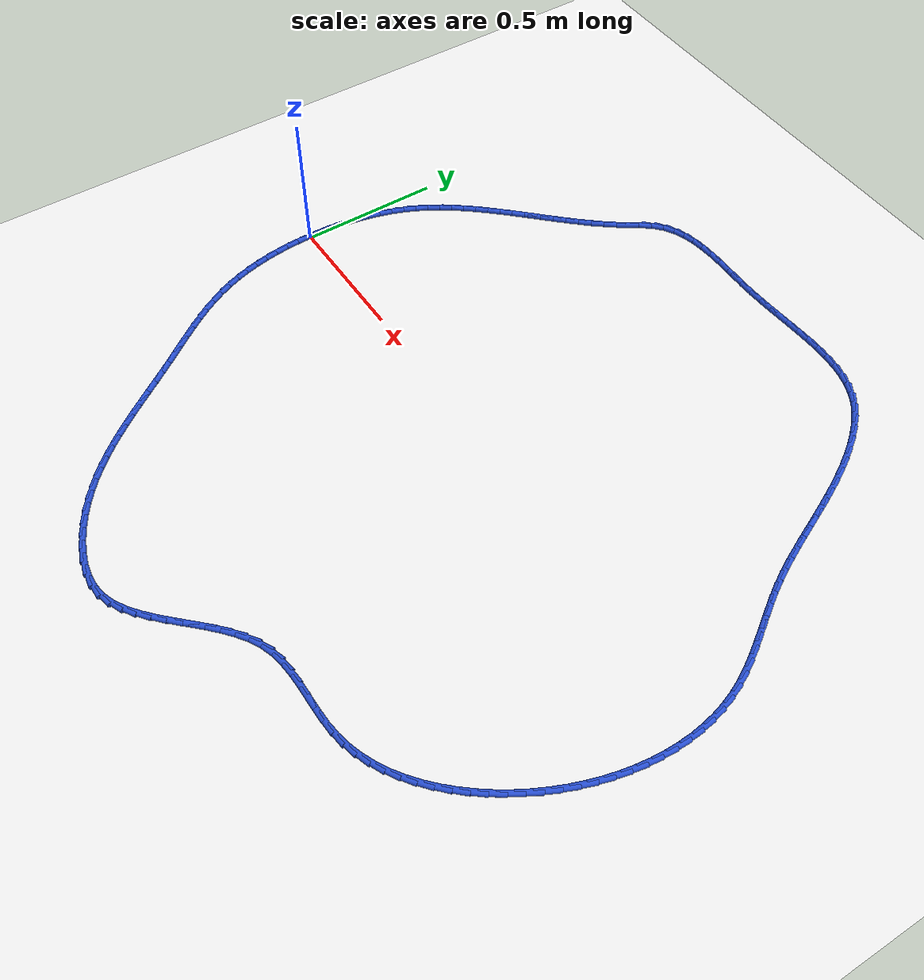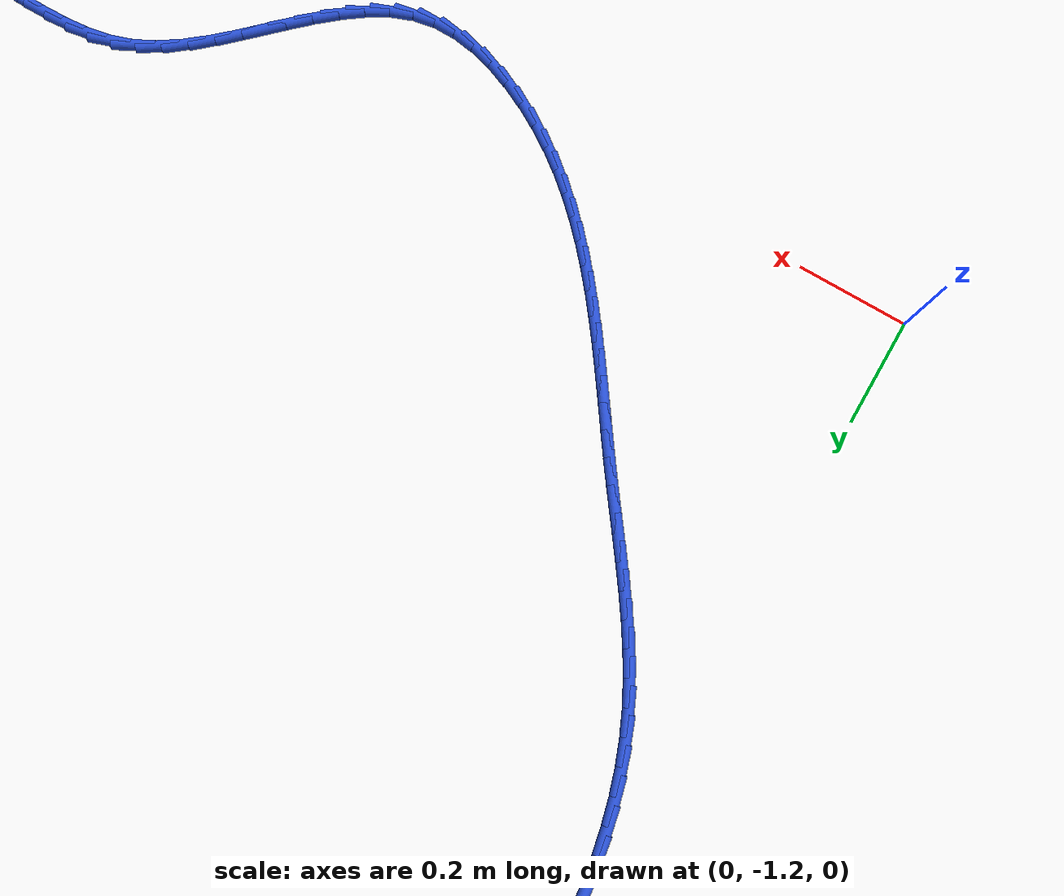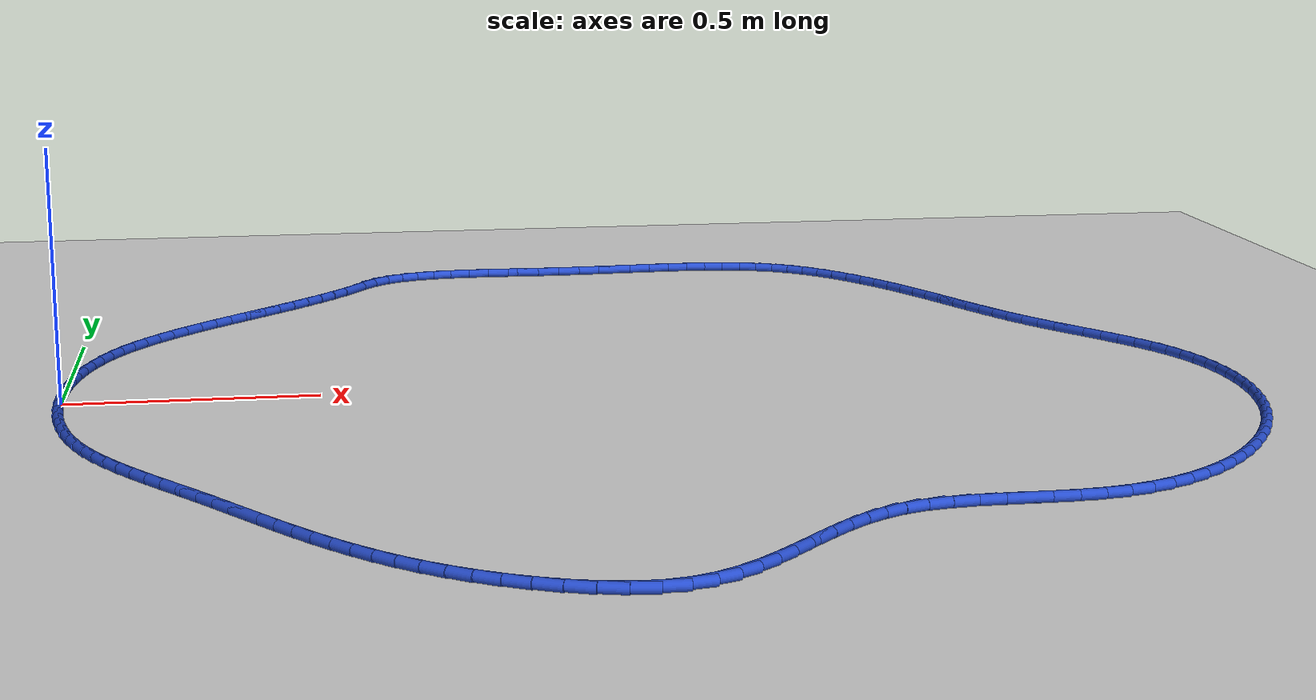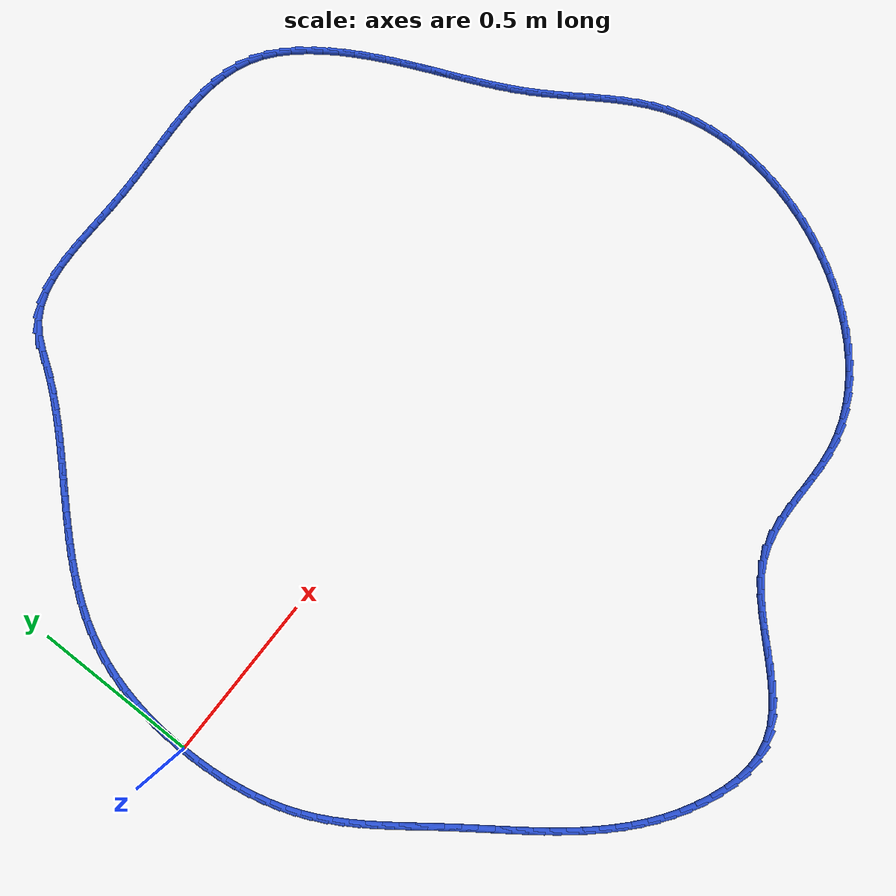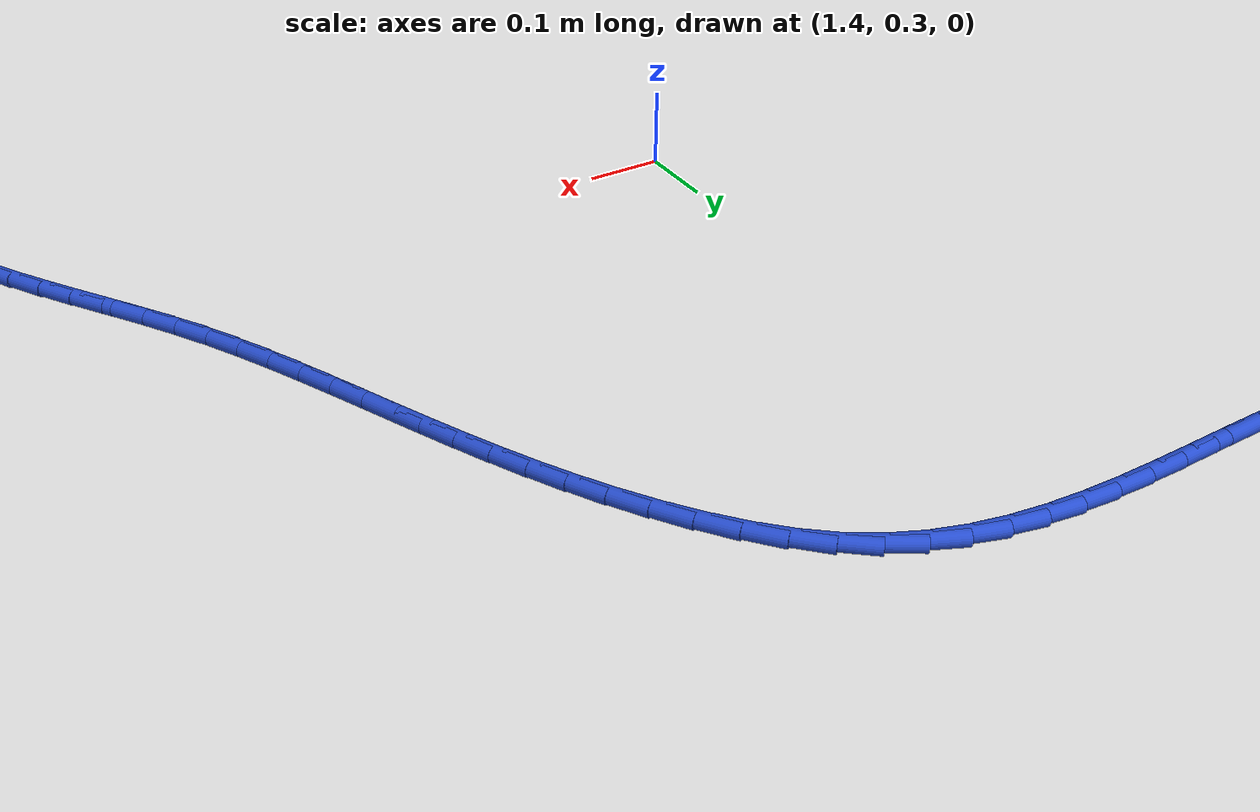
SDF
<sdf version="1.6">
 <world name="default">
  <light name="sun" type="directional">
   <pose>0 0 10 0 -0 0</pose>
   <diffuse>0.8 0.8 0.8 1</diffuse>
   <specular>0.2 0.2 0.2 1</specular>
   <attenuation>
    <range>1000</range>
    <constant>0.9</constant>
    <linear>0.01</linear>
    <quadratic>0.001</quadratic>
   </attenuation>
   <direction>-0.5 0.1 -0.9</direction>
  </light>
  <model name="ground_plane">
   <static>1</static>
   <link name="link">
    <collision name="collision">
     <geometry><plane><normal>0 0 1</normal><size>100 100</size></plane></geometry>
     <surface><friction><ode><mu>100</mu><mu2>50</mu2></ode></friction></surface>
    </collision>
    <visual name="visual">
     <cast_shadows>0</cast_shadows>
     <geometry><plane><normal>0 0 1</normal><size>100 100</size></plane></geometry>
     <material>
      <script><uri>file://media/materials/scripts/gazebo.material</uri><name>Gazebo/WhiteGlow</name></script>
     </material>
    </visual>
   </link>
  </model>
  <gravity>0 0 -9.8</gravity>
  <magnetic_field>6e-06 2.3e-05 -4.2e-05</magnetic_field>
  <atmosphere type="adiabatic"/>
  <physics name="default_physics" default="0" type="ode">
   <max_step_size>0.001</max_step_size>
   <real_time_factor>1</real_time_factor>
   <real_time_update_rate>1000</real_time_update_rate>
  </physics>
  <scene><ambient>0.4 0.4 0.4 1</ambient><background>0.7 0.7 0.7 1</background><shadows>1</shadows></scene>
  <spherical_coordinates>
   <surface_model>EARTH_WGS84</surface_model>
   <latitude_deg>0</latitude_deg>
   <longitude_deg>0</longitude_deg>
   <elevation>0</elevation>
   <heading_deg>0</heading_deg>
  </spherical_coordinates>
  <model name="line">
   <link name="link_0">
    <pose>1.5612511283791264e-17 -1.3877787807814457e-17 0.01 0 1.57 1.551756170840706</pose>
    <collision name="collision">
     <geometry><cylinder><radius>0.01</radius><length>0.08</length></cylinder></geometry>
    </collision>
    <visual name="visual">
     <material>
      <script><name>Gazebo/Blue</name><uri>file://media/materials/scripts/gazebo.material</uri></script>
     </material>
     <geometry><cylinder><radius>0.01</radius><length>0.08</length></cylinder></geometry>
    </visual>
   </link>
   <link name="link_1">
    <pose>0.0008938357104792639 0.0469390952818605 0.01 0 1.57 1.5104188653667308</pose>
    <collision name="collision">
     <geometry><cylinder><radius>0.01</radius><length>0.08</length></cylinder></geometry>
    </collision>
    <visual name="visual">
     <material>
      <script><name>Gazebo/Blue</name><uri>file://media/materials/scripts/gazebo.material</uri></script>
     </material>
     <geometry><cylinder><radius>0.01</radius><length>0.08</length></cylinder></geometry>
    </visual>
   </link>
   <link name="link_2">
    <pose>0.0037242009573501445 0.09375996248951225 0.01 0 1.57 1.4667045340990486</pose>
    <collision name="collision">
     <geometry><cylinder><radius>0.01</radius><length>0.08</length></cylinder></geometry>
    </collision>
    <visual name="visual">
     <material>
      <script><name>Gazebo/Blue</name><uri>file://media/materials/scripts/gazebo.material</uri></script>
     </material>
     <geometry><cylinder><radius>0.01</radius><length>0.08</length></cylinder></geometry>
    </visual>
   </link>
   <link name="link_3">
    <pose>0.008582734307786711 0.14026673280865445 0.01 0 1.57 1.4202309264281368</pose>
    <collision name="collision">
     <geometry><cylinder><radius>0.01</radius><length>0.08</length></cylinder></geometry>
    </collision>
    <visual name="visual">
     <material>
      <script><name>Gazebo/Blue</name><uri>file://media/materials/scripts/gazebo.material</uri></script>
     </material>
     <geometry><cylinder><radius>0.01</radius><length>0.08</length></cylinder></geometry>
    </visual>
   </link>
   <link name="link_4">
    <pose>0.015561074328962986 0.18626353742498628 0.01 0 1.57 1.3706086198448177</pose>
    <collision name="collision">
     <geometry><cylinder><radius>0.01</radius><length>0.08</length></cylinder></geometry>
    </collision>
    <visual name="visual">
     <material>
      <script><name>Gazebo/Blue</name><uri>file://media/materials/scripts/gazebo.material</uri></script>
     </material>
     <geometry><cylinder><radius>0.01</radius><length>0.08</length></cylinder></geometry>
    </visual>
   </link>
   <link name="link_5">
    <pose>0.024750859588053037 0.23155450752420698 0.01 0 1.57 1.3174485915538907</pose>
    <collision name="collision">
     <geometry><cylinder><radius>0.01</radius><length>0.08</length></cylinder></geometry>
    </collision>
    <visual name="visual">
     <material>
      <script><name>Gazebo/Blue</name><uri>file://media/materials/scripts/gazebo.material</uri></script>
     </material>
     <geometry><cylinder><radius>0.01</radius><length>0.08</length></cylinder></geometry>
    </visual>
   </link>
   <link name="link_6">
    <pose>0.03624372865223091 0.2759437742920158 0.01 0 1.57 1.26037590802754</pose>
    <collision name="collision">
     <geometry><cylinder><radius>0.01</radius><length>0.08</length></cylinder></geometry>
    </collision>
    <visual name="visual">
     <material>
      <script><name>Gazebo/Blue</name><uri>file://media/materials/scripts/gazebo.material</uri></script>
     </material>
     <geometry><cylinder><radius>0.01</radius><length>0.08</length></cylinder></geometry>
    </visual>
   </link>
   <link name="link_7">
    <pose>0.05013132008867062 0.319235468914112 0.01 0 1.57 1.1990511685747829</pose>
    <collision name="collision">
     <geometry><cylinder><radius>0.01</radius><length>0.08</length></cylinder></geometry>
    </collision>
    <visual name="visual">
     <material>
      <script><name>Gazebo/Blue</name><uri>file://media/materials/scripts/gazebo.material</uri></script>
     </material>
     <geometry><cylinder><radius>0.01</radius><length>0.08</length></cylinder></geometry>
    </visual>
   </link>
   <link name="link_8">
    <pose>0.06650527246454621 0.3612337225761945 0.01 0 1.57 1.1333860222953298</pose>
    <collision name="collision">
     <geometry><cylinder><radius>0.01</radius><length>0.08</length></cylinder></geometry>
    </collision>
    <visual name="visual">
     <material>
      <script><name>Gazebo/Blue</name><uri>file://media/materials/scripts/gazebo.material</uri></script>
     </material>
     <geometry><cylinder><radius>0.01</radius><length>0.08</length></cylinder></geometry>
    </visual>
   </link>
   <link name="link_9">
    <pose>0.08545114126222171 0.4017491837660959 0.01 0 1.57 1.0681659449033898</pose>
    <collision name="collision">
     <geometry><cylinder><radius>0.01</radius><length>0.08</length></cylinder></geometry>
    </collision>
    <visual name="visual">
     <material>
      <script><name>Gazebo/Blue</name><uri>file://media/materials/scripts/gazebo.material</uri></script>
     </material>
     <geometry><cylinder><radius>0.01</radius><length>0.08</length></cylinder></geometry>
    </visual>
   </link>
   <link name="link_10">
    <pose>0.10689696867808775 0.4407612577302191 0.01 0 1.57 1.009084838422873</pose>
    <collision name="collision">
     <geometry><cylinder><radius>0.01</radius><length>0.08</length></cylinder></geometry>
    </collision>
    <visual name="visual">
     <material>
      <script><name>Gazebo/Blue</name><uri>file://media/materials/scripts/gazebo.material</uri></script>
     </material>
     <geometry><cylinder><radius>0.01</radius><length>0.08</length></cylinder></geometry>
    </visual>
   </link>
   <link name="link_11">
    <pose>0.1306028356865399 0.4784293001947909 0.01 0 1.57 0.9568897960301141</pose>
    <collision name="collision">
     <geometry><cylinder><radius>0.01</radius><length>0.08</length></cylinder></geometry>
    </collision>
    <visual name="visual">
     <material>
      <script><name>Gazebo/Blue</name><uri>file://media/materials/scripts/gazebo.material</uri></script>
     </material>
     <geometry><cylinder><radius>0.01</radius><length>0.08</length></cylinder></geometry>
    </visual>
   </link>
   <link name="link_12">
    <pose>0.1563206478877656 0.5149214258275006 0.01 0 1.57 0.9118153678936415</pose>
    <collision name="collision">
     <geometry><cylinder><radius>0.01</radius><length>0.08</length></cylinder></geometry>
    </collision>
    <visual name="visual">
     <material>
      <script><name>Gazebo/Blue</name><uri>file://media/materials/scripts/gazebo.material</uri></script>
     </material>
     <geometry><cylinder><radius>0.01</radius><length>0.08</length></cylinder></geometry>
    </visual>
   </link>
   <link name="link_13">
    <pose>0.18380231088195215 0.5504057492960381 0.01 0 1.57 0.8739004066070336</pose>
    <collision name="collision">
     <geometry><cylinder><radius>0.01</radius><length>0.08</length></cylinder></geometry>
    </collision>
    <visual name="visual">
     <material>
      <script><name>Gazebo/Blue</name><uri>file://media/materials/scripts/gazebo.material</uri></script>
     </material>
     <geometry><cylinder><radius>0.01</radius><length>0.08</length></cylinder></geometry>
    </visual>
   </link>
   <link name="link_14">
    <pose>0.21279973026928706 0.5850503852680927 0.01 0 1.57 0.8430566126141176</pose>
    <collision name="collision">
     <geometry><cylinder><radius>0.01</radius><length>0.08</length></cylinder></geometry>
    </collision>
    <visual name="visual">
     <material>
      <script><name>Gazebo/Blue</name><uri>file://media/materials/scripts/gazebo.material</uri></script>
     </material>
     <geometry><cylinder><radius>0.01</radius><length>0.08</length></cylinder></geometry>
    </visual>
   </link>
   <link name="link_15">
    <pose>0.24306481164995766 0.619023448411354 0.01 0 1.57 0.8191276440051314</pose>
    <collision name="collision">
     <geometry><cylinder><radius>0.01</radius><length>0.08</length></cylinder></geometry>
    </collision>
    <visual name="visual">
     <material>
      <script><name>Gazebo/Blue</name><uri>file://media/materials/scripts/gazebo.material</uri></script>
     </material>
     <geometry><cylinder><radius>0.01</radius><length>0.08</length></cylinder></geometry>
    </visual>
   </link>
   <link name="link_16">
    <pose>0.27434946062415155 0.6524930533935118 0.01 0 1.57 0.8019349742027959</pose>
    <collision name="collision">
     <geometry><cylinder><radius>0.01</radius><length>0.08</length></cylinder></geometry>
    </collision>
    <visual name="visual">
     <material>
      <script><name>Gazebo/Blue</name><uri>file://media/materials/scripts/gazebo.material</uri></script>
     </material>
     <geometry><cylinder><radius>0.01</radius><length>0.08</length></cylinder></geometry>
    </visual>
   </link>
   <link name="link_17">
    <pose>0.30640558279205593 0.6856273148822553 0.01 0 1.57 0.7913104087051869</pose>
    <collision name="collision">
     <geometry><cylinder><radius>0.01</radius><length>0.08</length></cylinder></geometry>
    </collision>
    <visual name="visual">
     <material>
      <script><name>Gazebo/Blue</name><uri>file://media/materials/scripts/gazebo.material</uri></script>
     </material>
     <geometry><cylinder><radius>0.01</radius><length>0.08</length></cylinder></geometry>
    </visual>
   </link>
   <link name="link_18">
    <pose>0.33898508375385816 0.7185943475452742 0.01 0 1.57 0.7871169174299859</pose>
    <collision name="collision">
     <geometry><cylinder><radius>0.01</radius><length>0.08</length></cylinder></geometry>
    </collision>
    <visual name="visual">
     <material>
      <script><name>Gazebo/Blue</name><uri>file://media/materials/scripts/gazebo.material</uri></script>
     </material>
     <geometry><cylinder><radius>0.01</radius><length>0.08</length></cylinder></geometry>
    </visual>
   </link>
   <link name="link_19">
    <pose>0.371839869109746 0.7515622660502582 0.01 0 1.57 0.7892598214826891</pose>
    <collision name="collision">
     <geometry><cylinder><radius>0.01</radius><length>0.08</length></cylinder></geometry>
    </collision>
    <visual name="visual">
     <material>
      <script><name>Gazebo/Blue</name><uri>file://media/materials/scripts/gazebo.material</uri></script>
     </material>
     <geometry><cylinder><radius>0.01</radius><length>0.08</length></cylinder></geometry>
    </visual>
   </link>
   <link name="link_20">
    <pose>0.40472184445990644 0.7846991850648967 0.01 0 1.57 0.7976900060110687</pose>
    <collision name="collision">
     <geometry><cylinder><radius>0.01</radius><length>0.08</length></cylinder></geometry>
    </collision>
    <visual name="visual">
     <material>
      <script><name>Gazebo/Blue</name><uri>file://media/materials/scripts/gazebo.material</uri></script>
     </material>
     <geometry><cylinder><radius>0.01</radius><length>0.08</length></cylinder></geometry>
    </visual>
   </link>
   <link name="link_21">
    <pose>0.43738291540452723 0.8181732192568792 0.01 0 1.57 0.8124001498819933</pose>
    <collision name="collision">
     <geometry><cylinder><radius>0.01</radius><length>0.08</length></cylinder></geometry>
    </collision>
    <visual name="visual">
     <material>
      <script><name>Gazebo/Blue</name><uri>file://media/materials/scripts/gazebo.material</uri></script>
     </material>
     <geometry><cylinder><radius>0.01</radius><length>0.08</length></cylinder></geometry>
    </visual>
   </link>
   <link name="link_22">
    <pose>0.46957498754379556 0.8521524832938956 0.01 0 1.57 0.8334142381803004</pose>
    <collision name="collision">
     <geometry><cylinder><radius>0.01</radius><length>0.08</length></cylinder></geometry>
    </collision>
    <visual name="visual">
     <material>
      <script><name>Gazebo/Blue</name><uri>file://media/materials/scripts/gazebo.material</uri></script>
     </material>
     <geometry><cylinder><radius>0.01</radius><length>0.08</length></cylinder></geometry>
    </visual>
   </link>
   <link name="link_23">
    <pose>0.501049966477899 0.8868050918436352 0.01 0 1.57 0.8607700351608513</pose>
    <collision name="collision">
     <geometry><cylinder><radius>0.01</radius><length>0.08</length></cylinder></geometry>
    </collision>
    <visual name="visual">
     <material>
      <script><name>Gazebo/Blue</name><uri>file://media/materials/scripts/gazebo.material</uri></script>
     </material>
     <geometry><cylinder><radius>0.01</radius><length>0.08</length></cylinder></geometry>
    </visual>
   </link>
   <link name="link_24">
    <pose>0.5315597578070248 0.9222991595737873 0.01 0 1.57 0.8944939121003007</pose>
    <collision name="collision">
     <geometry><cylinder><radius>0.01</radius><length>0.08</length></cylinder></geometry>
    </collision>
    <visual name="visual">
     <material>
      <script><name>Gazebo/Blue</name><uri>file://media/materials/scripts/gazebo.material</uri></script>
     </material>
     <geometry><cylinder><radius>0.01</radius><length>0.08</length></cylinder></geometry>
    </visual>
   </link>
   <link name="link_25">
    <pose>0.5608562671313603 0.9588028011520418 0.01 0 1.57 0.9345676568104154</pose>
    <collision name="collision">
     <geometry><cylinder><radius>0.01</radius><length>0.08</length></cylinder></geometry>
    </collision>
    <visual name="visual">
     <material>
      <script><name>Gazebo/Blue</name><uri>file://media/materials/scripts/gazebo.material</uri></script>
     </material>
     <geometry><cylinder><radius>0.01</radius><length>0.08</length></cylinder></geometry>
    </visual>
   </link>
   <link name="link_26">
    <pose>0.5886914000510932 0.9964841312460881 0.01 0 1.57 0.9696095132786198</pose>
    <collision name="collision">
     <geometry><cylinder><radius>0.01</radius><length>0.08</length></cylinder></geometry>
    </collision>
    <visual name="visual">
     <material>
      <script><name>Gazebo/Blue</name><uri>file://media/materials/scripts/gazebo.material</uri></script>
     </material>
     <geometry><cylinder><radius>0.01</radius><length>0.08</length></cylinder></geometry>
    </visual>
   </link>
   <link name="link_27">
    <pose>0.6151438319806736 1.035051244932331 0.01 0 1.57 0.9143416901555427</pose>
    <collision name="collision">
     <geometry><cylinder><radius>0.01</radius><length>0.08</length></cylinder></geometry>
    </collision>
    <visual name="visual">
     <material>
      <script><name>Gazebo/Blue</name><uri>file://media/materials/scripts/gazebo.material</uri></script>
     </material>
     <geometry><cylinder><radius>0.01</radius><length>0.08</length></cylinder></geometry>
    </visual>
   </link>
   <link name="link_28">
    <pose>0.6427016946631761 1.0708202559378177 0.01 0 1.57 0.7356528513895213</pose>
    <collision name="collision">
     <geometry><cylinder><radius>0.01</radius><length>0.08</length></cylinder></geometry>
    </collision>
    <visual name="visual">
     <material>
      <script><name>Gazebo/Blue</name><uri>file://media/materials/scripts/gazebo.material</uri></script>
     </material>
     <geometry><cylinder><radius>0.01</radius><length>0.08</length></cylinder></geometry>
    </visual>
   </link>
   <link name="link_29">
    <pose>0.674351823088988 1.0994683536129373 0.01 0 1.57 0.5345600253316662</pose>
    <collision name="collision">
     <geometry><cylinder><radius>0.01</radius><length>0.08</length></cylinder></geometry>
    </collision>
    <visual name="visual">
     <material>
      <script><name>Gazebo/Blue</name><uri>file://media/materials/scripts/gazebo.material</uri></script>
     </material>
     <geometry><cylinder><radius>0.01</radius><length>0.08</length></cylinder></geometry>
    </visual>
   </link>
   <link name="link_30">
    <pose>0.7103663091396146 1.1207910521013569 0.01 0 1.57 0.36004748275417076</pose>
    <collision name="collision">
     <geometry><cylinder><radius>0.01</radius><length>0.08</length></cylinder></geometry>
    </collision>
    <visual name="visual">
     <material>
      <script><name>Gazebo/Blue</name><uri>file://media/materials/scripts/gazebo.material</uri></script>
     </material>
     <geometry><cylinder><radius>0.01</radius><length>0.08</length></cylinder></geometry>
    </visual>
   </link>
   <link name="link_31">
    <pose>0.7502194118248704 1.135794034076906 0.01 0 1.57 0.22080248202689576</pose>
    <collision name="collision">
     <geometry><cylinder><radius>0.01</radius><length>0.08</length></cylinder></geometry>
    </collision>
    <visual name="visual">
     <material>
      <script><name>Gazebo/Blue</name><uri>file://media/materials/scripts/gazebo.material</uri></script>
     </material>
     <geometry><cylinder><radius>0.01</radius><length>0.08</length></cylinder></geometry>
    </visual>
   </link>
   <link name="link_32">
    <pose>0.7933852858542295 1.1454831404182155 0.01 0 1.57 0.1165690919261657</pose>
    <collision name="collision">
     <geometry><cylinder><radius>0.01</radius><length>0.08</length></cylinder></geometry>
    </collision>
    <visual name="visual">
     <material>
      <script><name>Gazebo/Blue</name><uri>file://media/materials/scripts/gazebo.material</uri></script>
     </material>
     <geometry><cylinder><radius>0.01</radius><length>0.08</length></cylinder></geometry>
    </visual>
   </link>
   <link name="link_33">
    <pose>0.839338085937166 1.1508642120039152 0.01 0 1.57 0.04309113463695883</pose>
    <collision name="collision">
     <geometry><cylinder><radius>0.01</radius><length>0.08</length></cylinder></geometry>
    </collision>
    <visual name="visual">
     <material>
      <script><name>Gazebo/Blue</name><uri>file://media/materials/scripts/gazebo.material</uri></script>
     </material>
     <geometry><cylinder><radius>0.01</radius><length>0.08</length></cylinder></geometry>
    </visual>
   </link>
   <link name="link_34">
    <pose>0.8875519667831544 1.1529430897126365 0.01 0 1.57 -0.004353909167232691</pose>
    <collision name="collision">
     <geometry><cylinder><radius>0.01</radius><length>0.08</length></cylinder></geometry>
    </collision>
    <visual name="visual">
     <material>
      <script><name>Gazebo/Blue</name><uri>file://media/materials/scripts/gazebo.material</uri></script>
     </material>
     <geometry><cylinder><radius>0.01</radius><length>0.08</length></cylinder></geometry>
    </visual>
   </link>
   <link name="link_35">
    <pose>0.9375010831016684 1.1527256144230085 0.01 0 1.57 -0.029468234839879513</pose>
    <collision name="collision">
     <geometry><cylinder><radius>0.01</radius><length>0.08</length></cylinder></geometry>
    </collision>
    <visual name="visual">
     <material>
      <script><name>Gazebo/Blue</name><uri>file://media/materials/scripts/gazebo.material</uri></script>
     </material>
     <geometry><cylinder><radius>0.01</radius><length>0.08</length></cylinder></geometry>
    </visual>
   </link>
   <link name="link_36">
    <pose>0.9886595896021826 1.1512176270136625 0.01 0 1.57 -0.03456546580114034</pose>
    <collision name="collision">
     <geometry><cylinder><radius>0.01</radius><length>0.08</length></cylinder></geometry>
    </collision>
    <visual name="visual">
     <material>
      <script><name>Gazebo/Blue</name><uri>file://media/materials/scripts/gazebo.material</uri></script>
     </material>
     <geometry><cylinder><radius>0.01</radius><length>0.08</length></cylinder></geometry>
    </visual>
   </link>
   <link name="link_37">
    <pose>1.040501640994171 1.1494249683632283 0.01 0 1.57 -0.020602741015383185</pose>
    <collision name="collision">
     <geometry><cylinder><radius>0.01</radius><length>0.08</length></cylinder></geometry>
    </collision>
    <visual name="visual">
     <material>
      <script><name>Gazebo/Blue</name><uri>file://media/materials/scripts/gazebo.material</uri></script>
     </material>
     <geometry><cylinder><radius>0.01</radius><length>0.08</length></cylinder></geometry>
    </visual>
   </link>
   <link name="link_38">
    <pose>1.0925013919871074 1.1483534793503365 0.01 0 1.57 0.009245893207210342</pose>
    <collision name="collision">
     <geometry><cylinder><radius>0.01</radius><length>0.08</length></cylinder></geometry>
    </collision>
    <visual name="visual">
     <material>
      <script><name>Gazebo/Blue</name><uri>file://media/materials/scripts/gazebo.material</uri></script>
     </material>
     <geometry><cylinder><radius>0.01</radius><length>0.08</length></cylinder></geometry>
    </visual>
   </link>
   <link name="link_39">
    <pose>1.1441770604625157 1.1488312806777432 0.01 0 1.57 0.035479211586760914</pose>
    <collision name="collision">
     <geometry><cylinder><radius>0.01</radius><length>0.08</length></cylinder></geometry>
    </collision>
    <visual name="visual">
     <material>
      <script><name>Gazebo/Blue</name><uri>file://media/materials/scripts/gazebo.material</uri></script>
     </material>
     <geometry><cylinder><radius>0.01</radius><length>0.08</length></cylinder></geometry>
    </visual>
   </link>
   <link name="link_40">
    <pose>1.1953048358441025 1.1506460153495897 0.01 0 1.57 0.05073569828713031</pose>
    <collision name="collision">
     <geometry><cylinder><radius>0.01</radius><length>0.08</length></cylinder></geometry>
    </collision>
    <visual name="visual">
     <material>
      <script><name>Gazebo/Blue</name><uri>file://media/materials/scripts/gazebo.material</uri></script>
     </material>
     <geometry><cylinder><radius>0.01</radius><length>0.08</length></cylinder></geometry>
    </visual>
   </link>
   <link name="link_41">
    <pose>1.2457545065595481 1.1532078131163386 0.01 0 1.57 0.054707227208260774</pose>
    <collision name="collision">
     <geometry><cylinder><radius>0.01</radius><length>0.08</length></cylinder></geometry>
    </collision>
    <visual name="visual">
     <material>
      <script><name>Gazebo/Blue</name><uri>file://media/materials/scripts/gazebo.material</uri></script>
     </material>
     <geometry><cylinder><radius>0.01</radius><length>0.08</length></cylinder></geometry>
    </visual>
   </link>
   <link name="link_42">
    <pose>1.2953959924459302 1.1559262737143767 0.01 0 1.57 0.046876764439201545</pose>
    <collision name="collision">
     <geometry><cylinder><radius>0.01</radius><length>0.08</length></cylinder></geometry>
    </collision>
    <visual name="visual">
     <material>
      <script><name>Gazebo/Blue</name><uri>file://media/materials/scripts/gazebo.material</uri></script>
     </material>
     <geometry><cylinder><radius>0.01</radius><length>0.08</length></cylinder></geometry>
    </visual>
   </link>
   <link name="link_43">
    <pose>1.3440992133403278 1.1582109968800902 0.01 0 1.57 0.026457323632876544</pose>
    <collision name="collision">
     <geometry><cylinder><radius>0.01</radius><length>0.08</length></cylinder></geometry>
    </collision>
    <visual name="visual">
     <material>
      <script><name>Gazebo/Blue</name><uri>file://media/materials/scripts/gazebo.material</uri></script>
     </material>
     <geometry><cylinder><radius>0.01</radius><length>0.08</length></cylinder></geometry>
    </visual>
   </link>
   <link name="link_44">
    <pose>1.3917340890798193 1.1594715823498654 0.01 0 1.57 -0.007622150960910491</pose>
    <collision name="collision">
     <geometry><cylinder><radius>0.01</radius><length>0.08</length></cylinder></geometry>
    </collision>
    <visual name="visual">
     <material>
      <script><name>Gazebo/Blue</name><uri>file://media/materials/scripts/gazebo.material</uri></script>
     </material>
     <geometry><cylinder><radius>0.01</radius><length>0.08</length></cylinder></geometry>
    </visual>
   </link>
   <link name="link_45">
    <pose>1.4381705395014832 1.1591176298600883 0.01 0 1.57 -0.05666742512035592</pose>
    <collision name="collision">
     <geometry><cylinder><radius>0.01</radius><length>0.08</length></cylinder></geometry>
    </collision>
    <visual name="visual">
     <material>
      <script><name>Gazebo/Blue</name><uri>file://media/materials/scripts/gazebo.material</uri></script>
     </material>
     <geometry><cylinder><radius>0.01</radius><length>0.08</length></cylinder></geometry>
    </visual>
   </link>
   <link name="link_46">
    <pose>1.483278484442398 1.1565587391471448 0.01 0 1.57 -0.12205482158631852</pose>
    <collision name="collision">
     <geometry><cylinder><radius>0.01</radius><length>0.08</length></cylinder></geometry>
    </collision>
    <visual name="visual">
     <material>
      <script><name>Gazebo/Blue</name><uri>file://media/materials/scripts/gazebo.material</uri></script>
     </material>
     <geometry><cylinder><radius>0.01</radius><length>0.08</length></cylinder></geometry>
    </visual>
   </link>
   <link name="link_47">
    <pose>1.5269278437396416 1.1512045099474217 0.01 0 1.57 -0.20487862210858812</pose>
    <collision name="collision">
     <geometry><cylinder><radius>0.01</radius><length>0.08</length></cylinder></geometry>
    </collision>
    <visual name="visual">
     <material>
      <script><name>Gazebo/Blue</name><uri>file://media/materials/scripts/gazebo.material</uri></script>
     </material>
     <geometry><cylinder><radius>0.01</radius><length>0.08</length></cylinder></geometry>
    </visual>
   </link>
   <link name="link_48">
    <pose>1.5689885372302936 1.1424645419973052 0.01 0 1.57 -0.3053500909972815</pose>
    <collision name="collision">
     <geometry><cylinder><radius>0.01</radius><length>0.08</length></cylinder></geometry>
    </collision>
    <visual name="visual">
     <material>
      <script><name>Gazebo/Blue</name><uri>file://media/materials/scripts/gazebo.material</uri></script>
     </material>
     <geometry><cylinder><radius>0.01</radius><length>0.08</length></cylinder></geometry>
    </visual>
   </link>
   <link name="link_49">
    <pose>1.6093304847514314 1.1297484350331812 0.01 0 1.57 -0.4220054690578486</pose>
    <collision name="collision">
     <geometry><cylinder><radius>0.01</radius><length>0.08</length></cylinder></geometry>
    </collision>
    <visual name="visual">
     <material>
      <script><name>Gazebo/Blue</name><uri>file://media/materials/scripts/gazebo.material</uri></script>
     </material>
     <geometry><cylinder><radius>0.01</radius><length>0.08</length></cylinder></geometry>
    </visual>
   </link>
   <link name="link_50">
    <pose>1.647823606140134 1.1124657887914362 0.01 0 1.57 -0.5510310978147841</pose>
    <collision name="collision">
     <geometry><cylinder><radius>0.01</radius><length>0.08</length></cylinder></geometry>
    </collision>
    <visual name="visual">
     <material>
      <script><name>Gazebo/Blue</name><uri>file://media/materials/scripts/gazebo.material</uri></script>
     </material>
     <geometry><cylinder><radius>0.01</radius><length>0.08</length></cylinder></geometry>
    </visual>
   </link>
   <link name="link_51">
    <pose>1.6843378719896942 1.0900268669959559 0.01 0 1.57 -0.6789046960107836</pose>
    <collision name="collision">
     <geometry><cylinder><radius>0.01</radius><length>0.08</length></cylinder></geometry>
    </collision>
    <visual name="visual">
     <material>
      <script><name>Gazebo/Blue</name><uri>file://media/materials/scripts/gazebo.material</uri></script>
     </material>
     <geometry><cylinder><radius>0.01</radius><length>0.08</length></cylinder></geometry>
    </visual>
   </link>
   <link name="link_52">
    <pose>1.7187738462404958 1.0622421523449674 0.01 0 1.57 -0.7838795957503206</pose>
    <collision name="collision">
     <geometry><cylinder><radius>0.01</radius><length>0.08</length></cylinder></geometry>
    </collision>
    <visual name="visual">
     <material>
      <script><name>Gazebo/Blue</name><uri>file://media/materials/scripts/gazebo.material</uri></script>
     </material>
     <geometry><cylinder><radius>0.01</radius><length>0.08</length></cylinder></geometry>
    </visual>
   </link>
   <link name="link_53">
    <pose>1.7511144576082371 1.0299996149329005 0.01 0 1.57 -0.8670533304567966</pose>
    <collision name="collision">
     <geometry><cylinder><radius>0.01</radius><length>0.08</length></cylinder></geometry>
    </collision>
    <visual name="visual">
     <material>
      <script><name>Gazebo/Blue</name><uri>file://media/materials/scripts/gazebo.material</uri></script>
     </material>
     <geometry><cylinder><radius>0.01</radius><length>0.08</length></cylinder></geometry>
    </visual>
   </link>
   <link name="link_54">
    <pose>1.7813563551304692 0.9943667126730029 0.01 0 1.57 -0.9328322490496349</pose>
    <collision name="collision">
     <geometry><cylinder><radius>0.01</radius><length>0.08</length></cylinder></geometry>
    </collision>
    <visual name="visual">
     <material>
      <script><name>Gazebo/Blue</name><uri>file://media/materials/scripts/gazebo.material</uri></script>
     </material>
     <geometry><cylinder><radius>0.01</radius><length>0.08</length></cylinder></geometry>
    </visual>
   </link>
   <link name="link_55">
    <pose>1.8094961878447444 0.9564109034785224 0.01 0 1.57 -0.9848042373705735</pose>
    <collision name="collision">
     <geometry><cylinder><radius>0.01</radius><length>0.08</length></cylinder></geometry>
    </collision>
    <visual name="visual">
     <material>
      <script><name>Gazebo/Blue</name><uri>file://media/materials/scripts/gazebo.material</uri></script>
     </material>
     <geometry><cylinder><radius>0.01</radius><length>0.08</length></cylinder></geometry>
    </visual>
   </link>
   <link name="link_56">
    <pose>1.835536881352142 0.9171791939462519 0.01 0 1.57 -1.0279345670024131</pose>
    <collision name="collision">
     <geometry><cylinder><radius>0.01</radius><length>0.08</length></cylinder></geometry>
    </collision>
    <visual name="visual">
     <material>
      <script><name>Gazebo/Blue</name><uri>file://media/materials/scripts/gazebo.material</uri></script>
     </material>
     <geometry><cylinder><radius>0.01</radius><length>0.08</length></cylinder></geometry>
    </visual>
   </link>
   <link name="link_57">
    <pose>1.8596230573765498 0.8772568934027547 0.01 0 1.57 -1.0651123211707856</pose>
    <collision name="collision">
     <geometry><cylinder><radius>0.01</radius><length>0.08</length></cylinder></geometry>
    </collision>
    <visual name="visual">
     <material>
      <script><name>Gazebo/Blue</name><uri>file://media/materials/scripts/gazebo.material</uri></script>
     </material>
     <geometry><cylinder><radius>0.01</radius><length>0.08</length></cylinder></geometry>
    </visual>
   </link>
   <link name="link_58">
    <pose>1.8820395689228855 0.8367723868892146 0.01 0 1.57 -1.0960957585517523</pose>
    <collision name="collision">
     <geometry><cylinder><radius>0.01</radius><length>0.08</length></cylinder></geometry>
    </collision>
    <visual name="visual">
     <material>
      <script><name>Gazebo/Blue</name><uri>file://media/materials/scripts/gazebo.material</uri></script>
     </material>
     <geometry><cylinder><radius>0.01</radius><length>0.08</length></cylinder></geometry>
    </visual>
   </link>
   <link name="link_59">
    <pose>1.9030772525813238 0.7958345627596506 0.01 0 1.57 -1.1206374326432522</pose>
    <collision name="collision">
     <geometry><cylinder><radius>0.01</radius><length>0.08</length></cylinder></geometry>
    </collision>
    <visual name="visual">
     <material>
      <script><name>Gazebo/Blue</name><uri>file://media/materials/scripts/gazebo.material</uri></script>
     </material>
     <geometry><cylinder><radius>0.01</radius><length>0.08</length></cylinder></geometry>
    </visual>
   </link>
   <link name="link_60">
    <pose>1.9230269449420407 0.7545523093680802 0.01 0 1.57 -1.1385776247088553</pose>
    <collision name="collision">
     <geometry><cylinder><radius>0.01</radius><length>0.08</length></cylinder></geometry>
    </collision>
    <visual name="visual">
     <material>
      <script><name>Gazebo/Blue</name><uri>file://media/materials/scripts/gazebo.material</uri></script>
     </material>
     <geometry><cylinder><radius>0.01</radius><length>0.08</length></cylinder></geometry>
    </visual>
   </link>
   <link name="link_61">
    <pose>1.9421794825952112 0.7130345150685208 0.01 0 1.57 -1.1498167082078252</pose>
    <collision name="collision">
     <geometry><cylinder><radius>0.01</radius><length>0.08</length></cylinder></geometry>
    </collision>
    <visual name="visual">
     <material>
      <script><name>Gazebo/Blue</name><uri>file://media/materials/scripts/gazebo.material</uri></script>
     </material>
     <geometry><cylinder><radius>0.01</radius><length>0.08</length></cylinder></geometry>
    </visual>
   </link>
   <link name="link_62">
    <pose>1.9608257021310094 0.6713900682149909 0.01 0 1.57 -1.1542930377490592</pose>
    <collision name="collision">
     <geometry><cylinder><radius>0.01</radius><length>0.08</length></cylinder></geometry>
    </collision>
    <visual name="visual">
     <material>
      <script><name>Gazebo/Blue</name><uri>file://media/materials/scripts/gazebo.material</uri></script>
     </material>
     <geometry><cylinder><radius>0.01</radius><length>0.08</length></cylinder></geometry>
    </visual>
   </link>
   <link name="link_63">
    <pose>1.9792564401396116 0.6297278571615079 0.01 0 1.57 -1.1519684460144604</pose>
    <collision name="collision">
     <geometry><cylinder><radius>0.01</radius><length>0.08</length></cylinder></geometry>
    </collision>
    <visual name="visual">
     <material>
      <script><name>Gazebo/Blue</name><uri>file://media/materials/scripts/gazebo.material</uri></script>
     </material>
     <geometry><cylinder><radius>0.01</radius><length>0.08</length></cylinder></geometry>
    </visual>
   </link>
   <link name="link_64">
    <pose>1.9977625332111926 0.5881567702620903 0.01 0 1.57 -1.142822453347083</pose>
    <collision name="collision">
     <geometry><cylinder><radius>0.01</radius><length>0.08</length></cylinder></geometry>
    </collision>
    <visual name="visual">
     <material>
      <script><name>Gazebo/Blue</name><uri>file://media/materials/scripts/gazebo.material</uri></script>
     </material>
     <geometry><cylinder><radius>0.01</radius><length>0.08</length></cylinder></geometry>
    </visual>
   </link>
   <link name="link_65">
    <pose>2.016634817935927 0.5467856958707554 0.01 0 1.57 -1.1268557132546373</pose>
    <collision name="collision">
     <geometry><cylinder><radius>0.01</radius><length>0.08</length></cylinder></geometry>
    </collision>
    <visual name="visual">
     <material>
      <script><name>Gazebo/Blue</name><uri>file://media/materials/scripts/gazebo.material</uri></script>
     </material>
     <geometry><cylinder><radius>0.01</radius><length>0.08</length></cylinder></geometry>
    </visual>
   </link>
   <link name="link_66">
    <pose>2.03616413090399 0.5057235223415211 0.01 0 1.57 -1.1041028036911467</pose>
    <collision name="collision">
     <geometry><cylinder><radius>0.01</radius><length>0.08</length></cylinder></geometry>
    </collision>
    <visual name="visual">
     <material>
      <script><name>Gazebo/Blue</name><uri>file://media/materials/scripts/gazebo.material</uri></script>
     </material>
     <geometry><cylinder><radius>0.01</radius><length>0.08</length></cylinder></geometry>
    </visual>
   </link>
   <link name="link_67">
    <pose>2.056641308705558 0.4650791380284058 0.01 0 1.57 -1.0746539343591226</pose>
    <collision name="collision">
     <geometry><cylinder><radius>0.01</radius><length>0.08</length></cylinder></geometry>
    </collision>
    <visual name="visual">
     <material>
      <script><name>Gazebo/Blue</name><uri>file://media/materials/scripts/gazebo.material</uri></script>
     </material>
     <geometry><cylinder><radius>0.01</radius><length>0.08</length></cylinder></geometry>
    </visual>
   </link>
   <link name="link_68">
    <pose>2.0783571879308047 0.4249614312854266 0.01 0 1.57 -1.0388643337372512</pose>
    <collision name="collision">
     <geometry><cylinder><radius>0.01</radius><length>0.08</length></cylinder></geometry>
    </collision>
    <visual name="visual">
     <material>
      <script><name>Gazebo/Blue</name><uri>file://media/materials/scripts/gazebo.material</uri></script>
     </material>
     <geometry><cylinder><radius>0.01</radius><length>0.08</length></cylinder></geometry>
    </visual>
   </link>
   <link name="link_69">
    <pose>2.10159482177263 0.38547624244021034 0.01 0 1.57 -1.005188417917236</pose>
    <collision name="collision">
     <geometry><cylinder><radius>0.01</radius><length>0.08</length></cylinder></geometry>
    </collision>
    <visual name="visual">
     <material>
      <script><name>Gazebo/Blue</name><uri>file://media/materials/scripts/gazebo.material</uri></script>
     </material>
     <geometry><cylinder><radius>0.01</radius><length>0.08</length></cylinder></geometry>
    </visual>
   </link>
   <link name="link_70">
    <pose>2.126279766970009 0.34658941400349647 0.01 0 1.57 -0.984949922145394</pose>
    <collision name="collision">
     <geometry><cylinder><radius>0.01</radius><length>0.08</length></cylinder></geometry>
    </collision>
    <visual name="visual">
     <material>
      <script><name>Gazebo/Blue</name><uri>file://media/materials/scripts/gazebo.material</uri></script>
     </material>
     <geometry><cylinder><radius>0.01</radius><length>0.08</length></cylinder></geometry>
    </visual>
   </link>
   <link name="link_71">
    <pose>2.151838647935099 0.30807140350874235 0.01 0 1.57 -0.978713715411996</pose>
    <collision name="collision">
     <geometry><cylinder><radius>0.01</radius><length>0.08</length></cylinder></geometry>
    </collision>
    <visual name="visual">
     <material>
      <script><name>Gazebo/Blue</name><uri>file://media/materials/scripts/gazebo.material</uri></script>
     </material>
     <geometry><cylinder><radius>0.01</radius><length>0.08</length></cylinder></geometry>
    </visual>
   </link>
   <link name="link_72">
    <pose>2.1776610294827132 0.26967815572245235 0.01 0 1.57 -0.9863899905767575</pose>
    <collision name="collision">
     <geometry><cylinder><radius>0.01</radius><length>0.08</length></cylinder></geometry>
    </collision>
    <visual name="visual">
     <material>
      <script><name>Gazebo/Blue</name><uri>file://media/materials/scripts/gazebo.material</uri></script>
     </material>
     <geometry><cylinder><radius>0.01</radius><length>0.08</length></cylinder></geometry>
    </visual>
   </link>
   <link name="link_73">
    <pose>2.2031364764276673 0.2311656154111296 0.01 0 1.57 -1.008126030425088</pose>
    <collision name="collision">
     <geometry><cylinder><radius>0.01</radius><length>0.08</length></cylinder></geometry>
    </collision>
    <visual name="visual">
     <material>
      <script><name>Gazebo/Blue</name><uri>file://media/materials/scripts/gazebo.material</uri></script>
     </material>
     <geometry><cylinder><radius>0.01</radius><length>0.08</length></cylinder></geometry>
    </visual>
   </link>
   <link name="link_74">
    <pose>2.227654553584773 0.19228972734127844 0.01 0 1.57 -1.0442661581170414</pose>
    <collision name="collision">
     <geometry><cylinder><radius>0.01</radius><length>0.08</length></cylinder></geometry>
    </collision>
    <visual name="visual">
     <material>
      <script><name>Gazebo/Blue</name><uri>file://media/materials/scripts/gazebo.material</uri></script>
     </material>
     <geometry><cylinder><radius>0.01</radius><length>0.08</length></cylinder></geometry>
    </visual>
   </link>
   <link name="link_75">
    <pose>2.250604825768847 0.15280643627940232 0.01 0 1.57 -1.095227984009506</pose>
    <collision name="collision">
     <geometry><cylinder><radius>0.01</radius><length>0.08</length></cylinder></geometry>
    </collision>
    <visual name="visual">
     <material>
      <script><name>Gazebo/Blue</name><uri>file://media/materials/scripts/gazebo.material</uri></script>
     </material>
     <geometry><cylinder><radius>0.01</radius><length>0.08</length></cylinder></geometry>
    </visual>
   </link>
   <link name="link_76">
    <pose>2.2713768577947024 0.11247168699200452 0.01 0 1.57 -1.1612740941962623</pose>
    <collision name="collision">
     <geometry><cylinder><radius>0.01</radius><length>0.08</length></cylinder></geometry>
    </collision>
    <visual name="visual">
     <material>
      <script><name>Gazebo/Blue</name><uri>file://media/materials/scripts/gazebo.material</uri></script>
     </material>
     <geometry><cylinder><radius>0.01</radius><length>0.08</length></cylinder></geometry>
    </visual>
   </link>
   <link name="link_77">
    <pose>2.2893602144771537 0.07104142424558949 0.01 0 1.57 -1.2399183782324792</pose>
    <collision name="collision">
     <geometry><cylinder><radius>0.01</radius><length>0.08</length></cylinder></geometry>
    </collision>
    <visual name="visual">
     <material>
      <script><name>Gazebo/Blue</name><uri>file://media/materials/scripts/gazebo.material</uri></script>
     </material>
     <geometry><cylinder><radius>0.01</radius><length>0.08</length></cylinder></geometry>
    </visual>
   </link>
   <link name="link_78">
    <pose>2.304032964202529 0.028326756079102868 0.01 0 1.57 -1.3189186228771146</pose>
    <collision name="collision">
     <geometry><cylinder><radius>0.01</radius><length>0.08</length></cylinder></geometry>
    </collision>
    <visual name="visual">
     <material>
      <script><name>Gazebo/Blue</name><uri>file://media/materials/scripts/gazebo.material</uri></script>
     </material>
     <geometry><cylinder><radius>0.01</radius><length>0.08</length></cylinder></geometry>
    </visual>
   </link>
   <link name="link_79">
    <pose>2.3153309946196994 -0.015575855914104424 0.01 0 1.57 -1.394334365909763</pose>
    <collision name="collision">
     <geometry><cylinder><radius>0.01</radius><length>0.08</length></cylinder></geometry>
    </collision>
    <visual name="visual">
     <material>
      <script><name>Gazebo/Blue</name><uri>file://media/materials/scripts/gazebo.material</uri></script>
     </material>
     <geometry><cylinder><radius>0.01</radius><length>0.08</length></cylinder></geometry>
    </visual>
   </link>
   <link name="link_80">
    <pose>2.323337787706472 -0.06047795626926299 0.01 0 1.57 -1.4661962134425361</pose>
    <collision name="collision">
     <geometry><cylinder><radius>0.01</radius><length>0.08</length></cylinder></geometry>
    </collision>
    <visual name="visual">
     <material>
      <script><name>Gazebo/Blue</name><uri>file://media/materials/scripts/gazebo.material</uri></script>
     </material>
     <geometry><cylinder><radius>0.01</radius><length>0.08</length></cylinder></geometry>
    </visual>
   </link>
   <link name="link_81">
    <pose>2.328136897364009 -0.10619104469259136 0.01 0 1.57 -1.5346631598240679</pose>
    <collision name="collision">
     <geometry><cylinder><radius>0.01</radius><length>0.08</length></cylinder></geometry>
    </collision>
    <visual name="visual">
     <material>
      <script><name>Gazebo/Blue</name><uri>file://media/materials/scripts/gazebo.material</uri></script>
     </material>
     <geometry><cylinder><radius>0.01</radius><length>0.08</length></cylinder></geometry>
    </visual>
   </link>
   <link name="link_82">
    <pose>2.329811877493473 -0.15252662089030877 0.01 0 1.57 1.5416062401000117</pose>
    <collision name="collision">
     <geometry><cylinder><radius>0.01</radius><length>0.08</length></cylinder></geometry>
    </collision>
    <visual name="visual">
     <material>
      <script><name>Gazebo/Blue</name><uri>file://media/materials/scripts/gazebo.material</uri></script>
     </material>
     <geometry><cylinder><radius>0.01</radius><length>0.08</length></cylinder></geometry>
    </visual>
   </link>
   <link name="link_83">
    <pose>2.328446281996025 -0.19929618456863232 0.01 0 1.57 1.479112948693568</pose>
    <collision name="collision">
     <geometry><cylinder><radius>0.01</radius><length>0.08</length></cylinder></geometry>
    </collision>
    <visual name="visual">
     <material>
      <script><name>Gazebo/Blue</name><uri>file://media/materials/scripts/gazebo.material</uri></script>
     </material>
     <geometry><cylinder><radius>0.01</radius><length>0.08</length></cylinder></geometry>
    </visual>
   </link>
   <link name="link_84">
    <pose>2.3241236647728276 -0.24631123543378103 0.01 0 1.57 1.4190969305252579</pose>
    <collision name="collision">
     <geometry><cylinder><radius>0.01</radius><length>0.08</length></cylinder></geometry>
    </collision>
    <visual name="visual">
     <material>
      <script><name>Gazebo/Blue</name><uri>file://media/materials/scripts/gazebo.material</uri></script>
     </material>
     <geometry><cylinder><radius>0.01</radius><length>0.08</length></cylinder></geometry>
    </visual>
   </link>
   <link name="link_85">
    <pose>2.316927579725044 -0.2933832731919736 0.01 0 1.57 1.3611839267809676</pose>
    <collision name="collision">
     <geometry><cylinder><radius>0.01</radius><length>0.08</length></cylinder></geometry>
    </collision>
    <visual name="visual">
     <material>
      <script><name>Gazebo/Blue</name><uri>file://media/materials/scripts/gazebo.material</uri></script>
     </material>
     <geometry><cylinder><radius>0.01</radius><length>0.08</length></cylinder></geometry>
    </visual>
   </link>
   <link name="link_86">
    <pose>2.3069415807538363 -0.3403237975494286 0.01 0 1.57 1.3049900606232636</pose>
    <collision name="collision">
     <geometry><cylinder><radius>0.01</radius><length>0.08</length></cylinder></geometry>
    </collision>
    <visual name="visual">
     <material>
      <script><name>Gazebo/Blue</name><uri>file://media/materials/scripts/gazebo.material</uri></script>
     </material>
     <geometry><cylinder><radius>0.01</radius><length>0.08</length></cylinder></geometry>
    </visual>
   </link>
   <link name="link_87">
    <pose>2.2942492217603645 -0.3869443082123653 0.01 0 1.57 1.2501294041197348</pose>
    <collision name="collision">
     <geometry><cylinder><radius>0.01</radius><length>0.08</length></cylinder></geometry>
    </collision>
    <visual name="visual">
     <material>
      <script><name>Gazebo/Blue</name><uri>file://media/materials/scripts/gazebo.material</uri></script>
     </material>
     <geometry><cylinder><radius>0.01</radius><length>0.08</length></cylinder></geometry>
    </visual>
   </link>
   <link name="link_88">
    <pose>2.2789340566457934 -0.4330563048870006 0.01 0 1.57 1.1962182457895125</pose>
    <collision name="collision">
     <geometry><cylinder><radius>0.01</radius><length>0.08</length></cylinder></geometry>
    </collision>
    <visual name="visual">
     <material>
      <script><name>Gazebo/Blue</name><uri>file://media/materials/scripts/gazebo.material</uri></script>
     </material>
     <geometry><cylinder><radius>0.01</radius><length>0.08</length></cylinder></geometry>
    </visual>
   </link>
   <link name="link_89">
    <pose>2.2610796393112844 -0.47847128727955374 0.01 0 1.57 1.142877042445908</pose>
    <collision name="collision">
     <geometry><cylinder><radius>0.01</radius><length>0.08</length></cylinder></geometry>
    </collision>
    <visual name="visual">
     <material>
      <script><name>Gazebo/Blue</name><uri>file://media/materials/scripts/gazebo.material</uri></script>
     </material>
     <geometry><cylinder><radius>0.01</radius><length>0.08</length></cylinder></geometry>
    </visual>
   </link>
   <link name="link_90">
    <pose>2.2407695236579985 -0.5230007550962433 0.01 0 1.57 1.0897308969278872</pose>
    <collision name="collision">
     <geometry><cylinder><radius>0.01</radius><length>0.08</length></cylinder></geometry>
    </collision>
    <visual name="visual">
     <material>
      <script><name>Gazebo/Blue</name><uri>file://media/materials/scripts/gazebo.material</uri></script>
     </material>
     <geometry><cylinder><radius>0.01</radius><length>0.08</length></cylinder></geometry>
    </visual>
   </link>
   <link name="link_91">
    <pose>2.2180872635871 -0.566456208043288 0.01 0 1.57 1.03640927419584</pose>
    <collision name="collision">
     <geometry><cylinder><radius>0.01</radius><length>0.08</length></cylinder></geometry>
    </collision>
    <visual name="visual">
     <material>
      <script><name>Gazebo/Blue</name><uri>file://media/materials/scripts/gazebo.material</uri></script>
     </material>
     <geometry><cylinder><radius>0.01</radius><length>0.08</length></cylinder></geometry>
    </visual>
   </link>
   <link name="link_92">
    <pose>2.193116412999748 -0.6086491458269065 0.01 0 1.57 0.9824971063889345</pose>
    <collision name="collision">
     <geometry><cylinder><radius>0.01</radius><length>0.08</length></cylinder></geometry>
    </collision>
    <visual name="visual">
     <material>
      <script><name>Gazebo/Blue</name><uri>file://media/materials/scripts/gazebo.material</uri></script>
     </material>
     <geometry><cylinder><radius>0.01</radius><length>0.08</length></cylinder></geometry>
    </visual>
   </link>
   <link name="link_93">
    <pose>2.1659404736150427 -0.6493868688183145 0.01 0 1.57 0.9267895767003484</pose>
    <collision name="collision">
     <geometry><cylinder><radius>0.01</radius><length>0.08</length></cylinder></geometry>
    </collision>
    <visual name="visual">
     <material>
      <script><name>Gazebo/Blue</name><uri>file://media/materials/scripts/gazebo.material</uri></script>
     </material>
     <geometry><cylinder><radius>0.01</radius><length>0.08</length></cylinder></geometry>
    </visual>
   </link>
   <link name="link_94">
    <pose>2.1366421212733226 -0.6884102150593363 0.01 0 1.57 0.8680067684217831</pose>
    <collision name="collision">
     <geometry><cylinder><radius>0.01</radius><length>0.08</length></cylinder></geometry>
    </collision>
    <visual name="visual">
     <material>
      <script><name>Gazebo/Blue</name><uri>file://media/materials/scripts/gazebo.material</uri></script>
     </material>
     <geometry><cylinder><radius>0.01</radius><length>0.08</length></cylinder></geometry>
    </visual>
   </link>
   <link name="link_95">
    <pose>2.1053033721766967 -0.7254069384161237 0.01 0 1.57 0.8053977715013263</pose>
    <collision name="collision">
     <geometry><cylinder><radius>0.01</radius><length>0.08</length></cylinder></geometry>
    </collision>
    <visual name="visual">
     <material>
      <script><name>Gazebo/Blue</name><uri>file://media/materials/scripts/gazebo.material</uri></script>
     </material>
     <geometry><cylinder><radius>0.01</radius><length>0.08</length></cylinder></geometry>
    </visual>
   </link>
   <link name="link_96">
    <pose>2.0720062241207042 -0.7600633114917603 0.01 0 1.57 0.7382249399401939</pose>
    <collision name="collision">
     <geometry><cylinder><radius>0.01</radius><length>0.08</length></cylinder></geometry>
    </collision>
    <visual name="visual">
     <material>
      <script><name>Gazebo/Blue</name><uri>file://media/materials/scripts/gazebo.material</uri></script>
     </material>
     <geometry><cylinder><radius>0.01</radius><length>0.08</length></cylinder></geometry>
    </visual>
   </link>
   <link name="link_97">
    <pose>2.036832674900885 -0.7920656068893287 0.01 0 1.57 0.6657725497142223</pose>
    <collision name="collision">
     <geometry><cylinder><radius>0.01</radius><length>0.08</length></cylinder></geometry>
    </collision>
    <visual name="visual">
     <material>
      <script><name>Gazebo/Blue</name><uri>file://media/materials/scripts/gazebo.material</uri></script>
     </material>
     <geometry><cylinder><radius>0.01</radius><length>0.08</length></cylinder></geometry>
    </visual>
   </link>
   <link name="link_98">
    <pose>1.9998647223127755 -0.8211000972119121 0.01 0 1.57 0.5873947576112122</pose>
    <collision name="collision">
     <geometry><cylinder><radius>0.01</radius><length>0.08</length></cylinder></geometry>
    </collision>
    <visual name="visual">
     <material>
      <script><name>Gazebo/Blue</name><uri>file://media/materials/scripts/gazebo.material</uri></script>
     </material>
     <geometry><cylinder><radius>0.01</radius><length>0.08</length></cylinder></geometry>
    </visual>
   </link>
   <link name="link_99">
    <pose>1.961184364151915 -0.8468530550625941 0.01 0 1.57 0.5025913268602459</pose>
    <collision name="collision">
     <geometry><cylinder><radius>0.01</radius><length>0.08</length></cylinder></geometry>
    </collision>
    <visual name="visual">
     <material>
      <script><name>Gazebo/Blue</name><uri>file://media/materials/scripts/gazebo.material</uri></script>
     </material>
     <geometry><cylinder><radius>0.01</radius><length>0.08</length></cylinder></geometry>
    </visual>
   </link>
   <link name="link_100">
    <pose>1.9208735982138425 -0.8690107530444581 0.01 0 1.57 0.4111127923886655</pose>
    <collision name="collision">
     <geometry><cylinder><radius>0.01</radius><length>0.08</length></cylinder></geometry>
    </collision>
    <visual name="visual">
     <material>
      <script><name>Gazebo/Blue</name><uri>file://media/materials/scripts/gazebo.material</uri></script>
     </material>
     <geometry><cylinder><radius>0.01</radius><length>0.08</length></cylinder></geometry>
    </visual>
   </link>
   <link name="link_101">
    <pose>1.8790144222940943 -0.8872594637605872 0.01 0 1.57 0.3130870487203906</pose>
    <collision name="collision">
     <geometry><cylinder><radius>0.01</radius><length>0.08</length></cylinder></geometry>
    </collision>
    <visual name="visual">
     <material>
      <script><name>Gazebo/Blue</name><uri>file://media/materials/scripts/gazebo.material</uri></script>
     </material>
     <geometry><cylinder><radius>0.01</radius><length>0.08</length></cylinder></geometry>
    </visual>
   </link>
   <link name="link_102">
    <pose>1.8356888341882114 -0.9012854598140642 0.01 0 1.57 0.20915160846940364</pose>
    <collision name="collision">
     <geometry><cylinder><radius>0.01</radius><length>0.08</length></cylinder></geometry>
    </collision>
    <visual name="visual">
     <material>
      <script><name>Gazebo/Blue</name><uri>file://media/materials/scripts/gazebo.material</uri></script>
     </material>
     <geometry><cylinder><radius>0.01</radius><length>0.08</length></cylinder></geometry>
    </visual>
   </link>
   <link name="link_103">
    <pose>1.7909789120356556 -0.9107753943328168 0.01 0 1.57 0.10955299941121056</pose>
    <collision name="collision">
     <geometry><cylinder><radius>0.01</radius><length>0.08</length></cylinder></geometry>
    </collision>
    <visual name="visual">
     <material>
      <script><name>Gazebo/Blue</name><uri>file://media/materials/scripts/gazebo.material</uri></script>
     </material>
     <geometry><cylinder><radius>0.01</radius><length>0.08</length></cylinder></geometry>
    </visual>
   </link>
   <link name="link_104">
    <pose>1.74505350508198 -0.9158268856989105 0.01 0 1.57 0.040733349715306885</pose>
    <collision name="collision">
     <geometry><cylinder><radius>0.01</radius><length>0.08</length></cylinder></geometry>
    </collision>
    <visual name="visual">
     <material>
      <script><name>Gazebo/Blue</name><uri>file://media/materials/scripts/gazebo.material</uri></script>
     </material>
     <geometry><cylinder><radius>0.01</radius><length>0.08</length></cylinder></geometry>
    </visual>
   </link>
   <link name="link_105">
    <pose>1.6983334475482144 -0.9177310033653379 0.01 0 1.57 0.005594958672195666</pose>
    <collision name="collision">
     <geometry><cylinder><radius>0.01</radius><length>0.08</length></cylinder></geometry>
    </collision>
    <visual name="visual">
     <material>
      <script><name>Gazebo/Blue</name><uri>file://media/materials/scripts/gazebo.material</uri></script>
     </material>
     <geometry><cylinder><radius>0.01</radius><length>0.08</length></cylinder></geometry>
    </visual>
   </link>
   <link name="link_106">
    <pose>1.6512850580421445 -0.9179942399069706 0.01 0 1.57 0.00274667578630848</pose>
    <collision name="collision">
     <geometry><cylinder><radius>0.01</radius><length>0.08</length></cylinder></geometry>
    </collision>
    <visual name="visual">
     <material>
      <script><name>Gazebo/Blue</name><uri>file://media/materials/scripts/gazebo.material</uri></script>
     </material>
     <geometry><cylinder><radius>0.01</radius><length>0.08</length></cylinder></geometry>
    </visual>
   </link>
   <link name="link_107">
    <pose>1.6043746551715592 -0.9181230878986809 0.01 0 1.57 0.0324023566491863</pose>
    <collision name="collision">
     <geometry><cylinder><radius>0.01</radius><length>0.08</length></cylinder></geometry>
    </collision>
    <visual name="visual">
     <material>
      <script><name>Gazebo/Blue</name><uri>file://media/materials/scripts/gazebo.material</uri></script>
     </material>
     <geometry><cylinder><radius>0.01</radius><length>0.08</length></cylinder></geometry>
    </visual>
   </link>
   <link name="link_108">
    <pose>1.5580685575442432 -0.9196240399153405 0.01 0 1.57 0.09651587223530028</pose>
    <collision name="collision">
     <geometry><cylinder><radius>0.01</radius><length>0.08</length></cylinder></geometry>
    </collision>
    <visual name="visual">
     <material>
      <script><name>Gazebo/Blue</name><uri>file://media/materials/scripts/gazebo.material</uri></script>
     </material>
     <geometry><cylinder><radius>0.01</radius><length>0.08</length></cylinder></geometry>
    </visual>
   </link>
   <link name="link_109">
    <pose>1.512833083767984 -0.924003588531822 0.01 0 1.57 0.19794409065192045</pose>
    <collision name="collision">
     <geometry><cylinder><radius>0.01</radius><length>0.08</length></cylinder></geometry>
    </collision>
    <visual name="visual">
     <material>
      <script><name>Gazebo/Blue</name><uri>file://media/materials/scripts/gazebo.material</uri></script>
     </material>
     <geometry><cylinder><radius>0.01</radius><length>0.08</length></cylinder></geometry>
    </visual>
   </link>
   <link name="link_110">
    <pose>1.4691345524505675 -0.9327682263229967 0.01 0 1.57 0.33789011468176916</pose>
    <collision name="collision">
     <geometry><cylinder><radius>0.01</radius><length>0.08</length></cylinder></geometry>
    </collision>
    <visual name="visual">
     <material>
      <script><name>Gazebo/Blue</name><uri>file://media/materials/scripts/gazebo.material</uri></script>
     </material>
     <geometry><cylinder><radius>0.01</radius><length>0.08</length></cylinder></geometry>
    </visual>
   </link>
   <link name="link_111">
    <pose>1.4274376071111385 -0.9474190631038539 0.01 0 1.57 0.4924434628749308</pose>
    <collision name="collision">
     <geometry><cylinder><radius>0.01</radius><length>0.08</length></cylinder></geometry>
    </collision>
    <visual name="visual">
     <material>
      <script><name>Gazebo/Blue</name><uri>file://media/materials/scripts/gazebo.material</uri></script>
     </material>
     <geometry><cylinder><radius>0.01</radius><length>0.08</length></cylinder></geometry>
    </visual>
   </link>
   <link name="link_112">
    <pose>1.387942979684898 -0.9686091504721337 0.01 0 1.57 0.6154987719939531</pose>
    <collision name="collision">
     <geometry><cylinder><radius>0.01</radius><length>0.08</length></cylinder></geometry>
    </collision>
    <visual name="visual">
     <material>
      <script><name>Gazebo/Blue</name><uri>file://media/materials/scripts/gazebo.material</uri></script>
     </material>
     <geometry><cylinder><radius>0.01</radius><length>0.08</length></cylinder></geometry>
    </visual>
   </link>
   <link name="link_113">
    <pose>1.3503020860528079 -0.9952263579646173 0.01 0 1.57 0.703502328011055</pose>
    <collision name="collision">
     <geometry><cylinder><radius>0.01</radius><length>0.08</length></cylinder></geometry>
    </collision>
    <visual name="visual">
     <material>
      <script><name>Gazebo/Blue</name><uri>file://media/materials/scripts/gazebo.material</uri></script>
     </material>
     <geometry><cylinder><radius>0.01</radius><length>0.08</length></cylinder></geometry>
    </visual>
   </link>
   <link name="link_114">
    <pose>1.3140977768383182 -1.025938226289839 0.01 0 1.57 0.7604858901946682</pose>
    <collision name="collision">
     <geometry><cylinder><radius>0.01</radius><length>0.08</length></cylinder></geometry>
    </collision>
    <visual name="visual">
     <material>
      <script><name>Gazebo/Blue</name><uri>file://media/materials/scripts/gazebo.material</uri></script>
     </material>
     <geometry><cylinder><radius>0.01</radius><length>0.08</length></cylinder></geometry>
    </visual>
   </link>
   <link name="link_115">
    <pose>1.2789129026648791 -1.0594122961563337 0.01 0 1.57 0.7900209574443715</pose>
    <collision name="collision">
     <geometry><cylinder><radius>0.01</radius><length>0.08</length></cylinder></geometry>
    </collision>
    <visual name="visual">
     <material>
      <script><name>Gazebo/Blue</name><uri>file://media/materials/scripts/gazebo.material</uri></script>
     </material>
     <geometry><cylinder><radius>0.01</radius><length>0.08</length></cylinder></geometry>
    </visual>
   </link>
   <link name="link_116">
    <pose>1.2443303141559399 -1.0943161082726356 0.01 0 1.57 0.7940961499438406</pose>
    <collision name="collision">
     <geometry><cylinder><radius>0.01</radius><length>0.08</length></cylinder></geometry>
    </collision>
    <visual name="visual">
     <material>
      <script><name>Gazebo/Blue</name><uri>file://media/materials/scripts/gazebo.material</uri></script>
     </material>
     <geometry><cylinder><radius>0.01</radius><length>0.08</length></cylinder></geometry>
    </visual>
   </link>
   <link name="link_117">
    <pose>1.2099328619349516 -1.1293172033472778 0.01 0 1.57 0.7727730323567963</pose>
    <collision name="collision">
     <geometry><cylinder><radius>0.01</radius><length>0.08</length></cylinder></geometry>
    </collision>
    <visual name="visual">
     <material>
      <script><name>Gazebo/Blue</name><uri>file://media/materials/scripts/gazebo.material</uri></script>
     </material>
     <geometry><cylinder><radius>0.01</radius><length>0.08</length></cylinder></geometry>
    </visual>
   </link>
   <link name="link_118">
    <pose>1.1753033966253643 -1.1630831220887952 0.01 0 1.57 0.724095194638197</pose>
    <collision name="collision">
     <geometry><cylinder><radius>0.01</radius><length>0.08</length></cylinder></geometry>
    </collision>
    <visual name="visual">
     <material>
      <script><name>Gazebo/Blue</name><uri>file://media/materials/scripts/gazebo.material</uri></script>
     </material>
     <geometry><cylinder><radius>0.01</radius><length>0.08</length></cylinder></geometry>
    </visual>
   </link>
   <link name="link_119">
    <pose>1.1400247688506269 -1.1942814052057216 0.01 0 1.57 0.6441960132005059</pose>
    <collision name="collision">
     <geometry><cylinder><radius>0.01</radius><length>0.08</length></cylinder></geometry>
    </collision>
    <visual name="visual">
     <material>
      <script><name>Gazebo/Blue</name><uri>file://media/materials/scripts/gazebo.material</uri></script>
     </material>
     <geometry><cylinder><radius>0.01</radius><length>0.08</length></cylinder></geometry>
    </visual>
   </link>
   <link name="link_120">
    <pose>1.1036798292341905 -1.2215795934065914 0.01 0 1.57 0.5280560429068475</pose>
    <collision name="collision">
     <geometry><cylinder><radius>0.01</radius><length>0.08</length></cylinder></geometry>
    </collision>
    <visual name="visual">
     <material>
      <script><name>Gazebo/Blue</name><uri>file://media/materials/scripts/gazebo.material</uri></script>
     </material>
     <geometry><cylinder><radius>0.01</radius><length>0.08</length></cylinder></geometry>
    </visual>
   </link>
   <link name="link_121">
    <pose>1.0658514283995033 -1.2436452273999392 0.01 0 1.57 0.3719938376863075</pose>
    <collision name="collision">
     <geometry><cylinder><radius>0.01</radius><length>0.08</length></cylinder></geometry>
    </collision>
    <visual name="visual">
     <material>
      <script><name>Gazebo/Blue</name><uri>file://media/materials/scripts/gazebo.material</uri></script>
     </material>
     <geometry><cylinder><radius>0.01</radius><length>0.08</length></cylinder></geometry>
    </visual>
   </link>
   <link name="link_122">
    <pose>1.0261224169700178 -1.259145847894299 0.01 0 1.57 0.17968748972214715</pose>
    <collision name="collision">
     <geometry><cylinder><radius>0.01</radius><length>0.08</length></cylinder></geometry>
    </collision>
    <visual name="visual">
     <material>
      <script><name>Gazebo/Blue</name><uri>file://media/materials/scripts/gazebo.material</uri></script>
     </material>
     <geometry><cylinder><radius>0.01</radius><length>0.08</length></cylinder></geometry>
    </visual>
   </link>
   <link name="link_123">
    <pose>0.9840926769484483 -1.266780411008174 0.01 0 1.57 -0.010245193181587554</pose>
    <collision name="collision">
     <geometry><cylinder><radius>0.01</radius><length>0.08</length></cylinder></geometry>
    </collision>
    <visual name="visual">
     <material>
      <script><name>Gazebo/Blue</name><uri>file://media/materials/scripts/gazebo.material</uri></script>
     </material>
     <geometry><cylinder><radius>0.01</radius><length>0.08</length></cylinder></geometry>
    </visual>
   </link>
   <link name="link_124">
    <pose>0.9399477305492332 -1.266328121679516 0.01 0 1.57 -0.16244372925285985</pose>
    <collision name="collision">
     <geometry><cylinder><radius>0.01</radius><length>0.08</length></cylinder></geometry>
    </collision>
    <visual name="visual">
     <material>
      <script><name>Gazebo/Blue</name><uri>file://media/materials/scripts/gazebo.material</uri></script>
     </material>
     <geometry><cylinder><radius>0.01</radius><length>0.08</length></cylinder></geometry>
    </visual>
   </link>
   <link name="link_125">
    <pose>0.8945923749212104 -1.2588949310006443 0.01 0 1.57 -0.2822146402139752</pose>
    <collision name="collision">
     <geometry><cylinder><radius>0.01</radius><length>0.08</length></cylinder></geometry>
    </collision>
    <visual name="visual">
     <material>
      <script><name>Gazebo/Blue</name><uri>file://media/materials/scripts/gazebo.material</uri></script>
     </material>
     <geometry><cylinder><radius>0.01</radius><length>0.08</length></cylinder></geometry>
    </visual>
   </link>
   <link name="link_126">
    <pose>0.8489755199837148 -1.2456681587392164 0.01 0 1.57 -0.37784144735803976</pose>
    <collision name="collision">
     <geometry><cylinder><radius>0.01</radius><length>0.08</length></cylinder></geometry>
    </collision>
    <visual name="visual">
     <material>
      <script><name>Gazebo/Blue</name><uri>file://media/materials/scripts/gazebo.material</uri></script>
     </material>
     <geometry><cylinder><radius>0.01</radius><length>0.08</length></cylinder></geometry>
    </visual>
   </link>
   <link name="link_127">
    <pose>0.804046075656084 -1.2278351246628918 0.01 0 1.57 -0.45633325926498103</pose>
    <collision name="collision">
     <geometry><cylinder><radius>0.01</radius><length>0.08</length></cylinder></geometry>
    </collision>
    <visual name="visual">
     <material>
      <script><name>Gazebo/Blue</name><uri>file://media/materials/scripts/gazebo.material</uri></script>
     </material>
     <geometry><cylinder><radius>0.01</radius><length>0.08</length></cylinder></geometry>
    </visual>
   </link>
   <link name="link_128">
    <pose>0.7607524464846939 -1.206582705668294 0.01 0 1.57 -0.5247841771985446</pose>
    <collision name="collision">
     <geometry><cylinder><radius>0.01</radius><length>0.08</length></cylinder></geometry>
    </collision>
    <visual name="visual">
     <material>
      <script><name>Gazebo/Blue</name><uri>file://media/materials/scripts/gazebo.material</uri></script>
     </material>
     <geometry><cylinder><radius>0.01</radius><length>0.08</length></cylinder></geometry>
    </visual>
   </link>
   <link name="link_129">
    <pose>0.7197637830064931 -1.182853061340637 0.01 0 1.57 -0.5893820339817992</pose>
    <collision name="collision">
     <geometry><cylinder><radius>0.01</radius><length>0.08</length></cylinder></geometry>
    </collision>
    <visual name="visual">
     <material>
      <script><name>Gazebo/Blue</name><uri>file://media/materials/scripts/gazebo.material</uri></script>
     </material>
     <geometry><cylinder><radius>0.01</radius><length>0.08</length></cylinder></geometry>
    </visual>
   </link>
   <link name="link_130">
    <pose>0.6810070008034068 -1.1569379121076098 0.01 0 1.57 -0.6500197623348749</pose>
    <collision name="collision">
     <geometry><cylinder><radius>0.01</radius><length>0.08</length></cylinder></geometry>
    </collision>
    <visual name="visual">
     <material>
      <script><name>Gazebo/Blue</name><uri>file://media/materials/scripts/gazebo.material</uri></script>
     </material>
     <geometry><cylinder><radius>0.01</radius><length>0.08</length></cylinder></geometry>
    </visual>
   </link>
   <link name="link_131">
    <pose>0.6442870664424455 -1.129022111408239 0.01 0 1.57 -0.7059104689070501</pose>
    <collision name="collision">
     <geometry><cylinder><radius>0.01</radius><length>0.08</length></cylinder></geometry>
    </collision>
    <visual name="visual">
     <material>
      <script><name>Gazebo/Blue</name><uri>file://media/materials/scripts/gazebo.material</uri></script>
     </material>
     <geometry><cylinder><radius>0.01</radius><length>0.08</length></cylinder></geometry>
    </visual>
   </link>
   <link name="link_132">
    <pose>0.6094089464906216 -1.0992905126815544 0.01 0 1.57 -0.75647476626325</pose>
    <collision name="collision">
     <geometry><cylinder><radius>0.01</radius><length>0.08</length></cylinder></geometry>
    </collision>
    <visual name="visual">
     <material>
      <script><name>Gazebo/Blue</name><uri>file://media/materials/scripts/gazebo.material</uri></script>
     </material>
     <geometry><cylinder><radius>0.01</radius><length>0.08</length></cylinder></geometry>
    </visual>
   </link>
   <link name="link_133">
    <pose>0.5761776075149465 -1.067927969366584 0.01 0 1.57 -0.801329178065593</pose>
    <collision name="collision">
     <geometry><cylinder><radius>0.01</radius><length>0.08</length></cylinder></geometry>
    </collision>
    <visual name="visual">
     <material>
      <script><name>Gazebo/Blue</name><uri>file://media/materials/scripts/gazebo.material</uri></script>
     </material>
     <geometry><cylinder><radius>0.01</radius><length>0.08</length></cylinder></geometry>
    </visual>
   </link>
   <link name="link_134">
    <pose>0.5443980160824311 -1.0351193349023553 0.01 0 1.57 -0.840256271199162</pose>
    <collision name="collision">
     <geometry><cylinder><radius>0.01</radius><length>0.08</length></cylinder></geometry>
    </collision>
    <visual name="visual">
     <material>
      <script><name>Gazebo/Blue</name><uri>file://media/materials/scripts/gazebo.material</uri></script>
     </material>
     <geometry><cylinder><radius>0.01</radius><length>0.08</length></cylinder></geometry>
    </visual>
   </link>
   <link name="link_135">
    <pose>0.5138751387600871 -1.0010494627278974 0.01 0 1.57 -0.8731659724002518</pose>
    <collision name="collision">
     <geometry><cylinder><radius>0.01</radius><length>0.08</length></cylinder></geometry>
    </collision>
    <visual name="visual">
     <material>
      <script><name>Gazebo/Blue</name><uri>file://media/materials/scripts/gazebo.material</uri></script>
     </material>
     <geometry><cylinder><radius>0.01</radius><length>0.08</length></cylinder></geometry>
    </visual>
   </link>
   <link name="link_136">
    <pose>0.4844139421149253 -0.9659032062822378 0.01 0 1.57 -0.9000558166777489</pose>
    <collision name="collision">
     <geometry><cylinder><radius>0.01</radius><length>0.08</length></cylinder></geometry>
    </collision>
    <visual name="visual">
     <material>
      <script><name>Gazebo/Blue</name><uri>file://media/materials/scripts/gazebo.material</uri></script>
     </material>
     <geometry><cylinder><radius>0.01</radius><length>0.08</length></cylinder></geometry>
    </visual>
   </link>
   <link name="link_137">
    <pose>0.45581939271395805 -0.9298654190044054 0.01 0 1.57 -0.9209751746489222</pose>
    <collision name="collision">
     <geometry><cylinder><radius>0.01</radius><length>0.08</length></cylinder></geometry>
    </collision>
    <visual name="visual">
     <material>
      <script><name>Gazebo/Blue</name><uri>file://media/materials/scripts/gazebo.material</uri></script>
     </material>
     <geometry><cylinder><radius>0.01</radius><length>0.08</length></cylinder></geometry>
    </visual>
   </link>
   <link name="link_138">
    <pose>0.42789645712419655 -0.8931209543334285 0.01 0 1.57 -0.9359959850813742</pose>
    <collision name="collision">
     <geometry><cylinder><radius>0.01</radius><length>0.08</length></cylinder></geometry>
    </collision>
    <visual name="visual">
     <material>
      <script><name>Gazebo/Blue</name><uri>file://media/materials/scripts/gazebo.material</uri></script>
     </material>
     <geometry><cylinder><radius>0.01</radius><length>0.08</length></cylinder></geometry>
    </visual>
   </link>
   <link name="link_139">
    <pose>0.40045010191265196 -0.8558546657083352 0.01 0 1.57 -0.945190723614473</pose>
    <collision name="collision">
     <geometry><cylinder><radius>0.01</radius><length>0.08</length></cylinder></geometry>
    </collision>
    <visual name="visual">
     <material>
      <script><name>Gazebo/Blue</name><uri>file://media/materials/scripts/gazebo.material</uri></script>
     </material>
     <geometry><cylinder><radius>0.01</radius><length>0.08</length></cylinder></geometry>
    </visual>
   </link>
   <link name="link_140">
    <pose>0.3732852936463357 -0.8182514065681535 0.01 0 1.57 -0.9486173398042885</pose>
    <collision name="collision">
     <geometry><cylinder><radius>0.01</radius><length>0.08</length></cylinder></geometry>
    </collision>
    <visual name="visual">
     <material>
      <script><name>Gazebo/Blue</name><uri>file://media/materials/scripts/gazebo.material</uri></script>
     </material>
     <geometry><cylinder><radius>0.01</radius><length>0.08</length></cylinder></geometry>
    </visual>
   </link>
   <link name="link_141">
    <pose>0.3462069988922588 -0.7804960303519112 0.01 0 1.57 -0.9463105286339023</pose>
    <collision name="collision">
     <geometry><cylinder><radius>0.01</radius><length>0.08</length></cylinder></geometry>
    </collision>
    <visual name="visual">
     <material>
      <script><name>Gazebo/Blue</name><uri>file://media/materials/scripts/gazebo.material</uri></script>
     </material>
     <geometry><cylinder><radius>0.01</radius><length>0.08</length></cylinder></geometry>
    </visual>
   </link>
   <link name="link_142">
    <pose>0.3190201842174336 -0.742773390498638 0.01 0 1.57 -0.9382790357689641</pose>
    <collision name="collision">
     <geometry><cylinder><radius>0.01</radius><length>0.08</length></cylinder></geometry>
    </collision>
    <visual name="visual">
     <material>
      <script><name>Gazebo/Blue</name><uri>file://media/materials/scripts/gazebo.material</uri></script>
     </material>
     <geometry><cylinder><radius>0.01</radius><length>0.08</length></cylinder></geometry>
    </visual>
   </link>
   <link name="link_143">
    <pose>0.29152982718920817 -0.7052683328648294 0.01 0 1.57 -0.9272873078355498</pose>
    <collision name="collision">
     <geometry><cylinder><radius>0.01</radius><length>0.08</length></cylinder></geometry>
    </collision>
    <visual name="visual">
     <material>
      <script><name>Gazebo/Blue</name><uri>file://media/materials/scripts/gazebo.material</uri></script>
     </material>
     <geometry><cylinder><radius>0.01</radius><length>0.08</length></cylinder></geometry>
    </visual>
   </link>
   <link name="link_144">
    <pose>0.26364736076539125 -0.6680923236125554 0.01 0 1.57 -0.9229141755954755</pose>
    <collision name="collision">
     <geometry><cylinder><radius>0.01</radius><length>0.08</length></cylinder></geometry>
    </collision>
    <visual name="visual">
     <material>
      <script><name>Gazebo/Blue</name><uri>file://media/materials/scripts/gazebo.material</uri></script>
     </material>
     <geometry><cylinder><radius>0.01</radius><length>0.08</length></cylinder></geometry>
    </visual>
   </link>
   <link name="link_145">
    <pose>0.23565171446122687 -0.6311035135483106 0.01 0 1.57 -0.9272590434008481</pose>
    <collision name="collision">
     <geometry><cylinder><radius>0.01</radius><length>0.08</length></cylinder></geometry>
    </collision>
    <visual name="visual">
     <material>
      <script><name>Gazebo/Blue</name><uri>file://media/materials/scripts/gazebo.material</uri></script>
     </material>
     <geometry><cylinder><radius>0.01</radius><length>0.08</length></cylinder></geometry>
    </visual>
   </link>
   <link name="link_146">
    <pose>0.20790106123893665 -0.5941054309752143 0.01 0 1.57 -0.9404168521874837</pose>
    <collision name="collision">
     <geometry><cylinder><radius>0.01</radius><length>0.08</length></cylinder></geometry>
    </collision>
    <visual name="visual">
     <material>
      <script><name>Gazebo/Blue</name><uri>file://media/materials/scripts/gazebo.material</uri></script>
     </material>
     <geometry><cylinder><radius>0.01</radius><length>0.08</length></cylinder></geometry>
    </visual>
   </link>
   <link name="link_147">
    <pose>0.1807535740607435 -0.5569016041963883 0.01 0 1.57 -0.9625389080568817</pose>
    <collision name="collision">
     <geometry><cylinder><radius>0.01</radius><length>0.08</length></cylinder></geometry>
    </collision>
    <visual name="visual">
     <material>
      <script><name>Gazebo/Blue</name><uri>file://media/materials/scripts/gazebo.material</uri></script>
     </material>
     <geometry><cylinder><radius>0.01</radius><length>0.08</length></cylinder></geometry>
    </visual>
   </link>
   <link name="link_148">
    <pose>0.15456742588886918 -0.5192955615149525 0.01 0 1.57 -0.9938038039409289</pose>
    <collision name="collision">
     <geometry><cylinder><radius>0.01</radius><length>0.08</length></cylinder></geometry>
    </collision>
    <visual name="visual">
     <material>
      <script><name>Gazebo/Blue</name><uri>file://media/materials/scripts/gazebo.material</uri></script>
     </material>
     <geometry><cylinder><radius>0.01</radius><length>0.08</length></cylinder></geometry>
    </visual>
   </link>
   <link name="link_149">
    <pose>0.1297007896855357 -0.48109083123402707 0.01 0 1.57 -1.034364132434718</pose>
    <collision name="collision">
     <geometry><cylinder><radius>0.01</radius><length>0.08</length></cylinder></geometry>
    </collision>
    <visual name="visual">
     <material>
      <script><name>Gazebo/Blue</name><uri>file://media/materials/scripts/gazebo.material</uri></script>
     </material>
     <geometry><cylinder><radius>0.01</radius><length>0.08</length></cylinder></geometry>
    </visual>
   </link>
   <link name="link_150">
    <pose>0.10651183841296523 -0.4420909416567325 0.01 0 1.57 -1.0842660736510992</pose>
    <collision name="collision">
     <geometry><cylinder><radius>0.01</radius><length>0.08</length></cylinder></geometry>
    </collision>
    <visual name="visual">
     <material>
      <script><name>Gazebo/Blue</name><uri>file://media/materials/scripts/gazebo.material</uri></script>
     </material>
     <geometry><cylinder><radius>0.01</radius><length>0.08</length></cylinder></geometry>
    </visual>
   </link>
   <link name="link_151">
    <pose>0.08535874503337954 -0.40209942108618846 0.01 0 1.57 -1.143054304727803</pose>
    <collision name="collision">
     <geometry><cylinder><radius>0.01</radius><length>0.08</length></cylinder></geometry>
    </collision>
    <visual name="visual">
     <material>
      <script><name>Gazebo/Blue</name><uri>file://media/materials/scripts/gazebo.material</uri></script>
     </material>
     <geometry><cylinder><radius>0.01</radius><length>0.08</length></cylinder></geometry>
    </visual>
   </link>
   <link name="link_152">
    <pose>0.0665890325712859 -0.3609279241225143 0.01 0 1.57 -1.2044378417835333</pose>
    <collision name="collision">
     <geometry><cylinder><radius>0.01</radius><length>0.08</length></cylinder></geometry>
    </collision>
    <visual name="visual">
     <material>
      <script><name>Gazebo/Blue</name><uri>file://media/materials/scripts/gazebo.material</uri></script>
     </material>
     <geometry><cylinder><radius>0.01</radius><length>0.08</length></cylinder></geometry>
    </visual>
   </link>
   <link name="link_153">
    <pose>0.05033142347921377 -0.31855505830758674 0.01 0 1.57 -1.2627340432484286</pose>
    <collision name="collision">
     <geometry><cylinder><radius>0.01</radius><length>0.08</length></cylinder></geometry>
    </collision>
    <visual name="visual">
     <material>
      <script><name>Gazebo/Blue</name><uri>file://media/materials/scripts/gazebo.material</uri></script>
     </material>
     <geometry><cylinder><radius>0.01</radius><length>0.08</length></cylinder></geometry>
    </visual>
   </link>
   <link name="link_154">
    <pose>0.036509450007719164 -0.27511599890854144 0.01 0 1.57 -1.3177782776932168</pose>
    <collision name="collision">
     <geometry><cylinder><radius>0.01</radius><length>0.08</length></cylinder></geometry>
    </collision>
    <visual name="visual">
     <material>
      <script><name>Gazebo/Blue</name><uri>file://media/materials/scripts/gazebo.material</uri></script>
     </material>
     <geometry><cylinder><radius>0.01</radius><length>0.08</length></cylinder></geometry>
    </visual>
   </link>
   <link name="link_155">
    <pose>0.02503872006375065 -0.23075196776023893 0.01 0 1.57 -1.3696908956653842</pose>
    <collision name="collision">
     <geometry><cylinder><radius>0.01</radius><length>0.08</length></cylinder></geometry>
    </collision>
    <visual name="visual">
     <material>
      <script><name>Gazebo/Blue</name><uri>file://media/materials/scripts/gazebo.material</uri></script>
     </material>
     <geometry><cylinder><radius>0.01</radius><length>0.08</length></cylinder></geometry>
    </visual>
   </link>
   <link name="link_156">
    <pose>0.01583484155425669 -0.1856041866975395 0.01 0 1.57 -1.4186429129163842</pose>
    <collision name="collision">
     <geometry><cylinder><radius>0.01</radius><length>0.08</length></cylinder></geometry>
    </collision>
    <visual name="visual">
     <material>
      <script><name>Gazebo/Blue</name><uri>file://media/materials/scripts/gazebo.material</uri></script>
     </material>
     <geometry><cylinder><radius>0.01</radius><length>0.08</length></cylinder></geometry>
    </visual>
   </link>
   <link name="link_157">
    <pose>0.008813422386186171 -0.1398138775553055 0.01 0 1.57 -1.4648394814556747</pose>
    <collision name="collision">
     <geometry><cylinder><radius>0.01</radius><length>0.08</length></cylinder></geometry>
    </collision>
    <visual name="visual">
     <material>
      <script><name>Gazebo/Blue</name><uri>file://media/materials/scripts/gazebo.material</uri></script>
     </material>
     <geometry><cylinder><radius>0.01</radius><length>0.08</length></cylinder></geometry>
    </visual>
   </link>
   <link name="link_158">
    <pose>0.0038900704664874995 -0.09352226216839694 0.01 0 1.57 -1.5085067931892449</pose>
    <collision name="collision">
     <geometry><cylinder><radius>0.01</radius><length>0.08</length></cylinder></geometry>
    </collision>
    <visual name="visual">
     <material>
      <script><name>Gazebo/Blue</name><uri>file://media/materials/scripts/gazebo.material</uri></script>
     </material>
     <geometry><cylinder><radius>0.01</radius><length>0.08</length></cylinder></geometry>
    </visual>
   </link>
   <link name="link_159">
    <pose>0.0009803937021092522 -0.046870562371674765 0.01 0 1.57 -1.5498823307066043</pose>
    <collision name="collision">
     <geometry><cylinder><radius>0.01</radius><length>0.08</length></cylinder></geometry>
    </collision>
    <visual name="visual">
     <material>
      <script><name>Gazebo/Blue</name><uri>file://media/materials/scripts/gazebo.material</uri></script>
     </material>
     <geometry><cylinder><radius>0.01</radius><length>0.08</length></cylinder></geometry>
    </visual>
   </link>
   <link name="link_160">
    <pose>3.469446951953614e-18 2.498001805406602e-16 0.01 0 1.57 1.5523845554950269</pose>
    <collision name="collision">
     <geometry><cylinder><radius>0.01</radius><length>0.08</length></cylinder></geometry>
    </collision>
    <visual name="visual">
     <material>
      <script><name>Gazebo/Blue</name><uri>file://media/materials/scripts/gazebo.material</uri></script>
     </material>
     <geometry><cylinder><radius>0.01</radius><length>0.08</length></cylinder></geometry>
    </visual>
   </link>
   <link name="link_161">
    <pose>0.0008644972671083707 0.0469482031117681 0.01 0 1.57 1.5523845554950273</pose>
    <collision name="collision">
     <geometry><cylinder><radius>0.01</radius><length>0.08</length></cylinder></geometry>
    </collision>
    <visual name="visual">
     <material>
      <script><name>Gazebo/Blue</name><uri>file://media/materials/scripts/gazebo.material</uri></script>
     </material>
     <geometry><cylinder><radius>0.01</radius><length>0.08</length></cylinder></geometry>
    </visual>
   </link>
  </model>
 </world>
</sdf>
